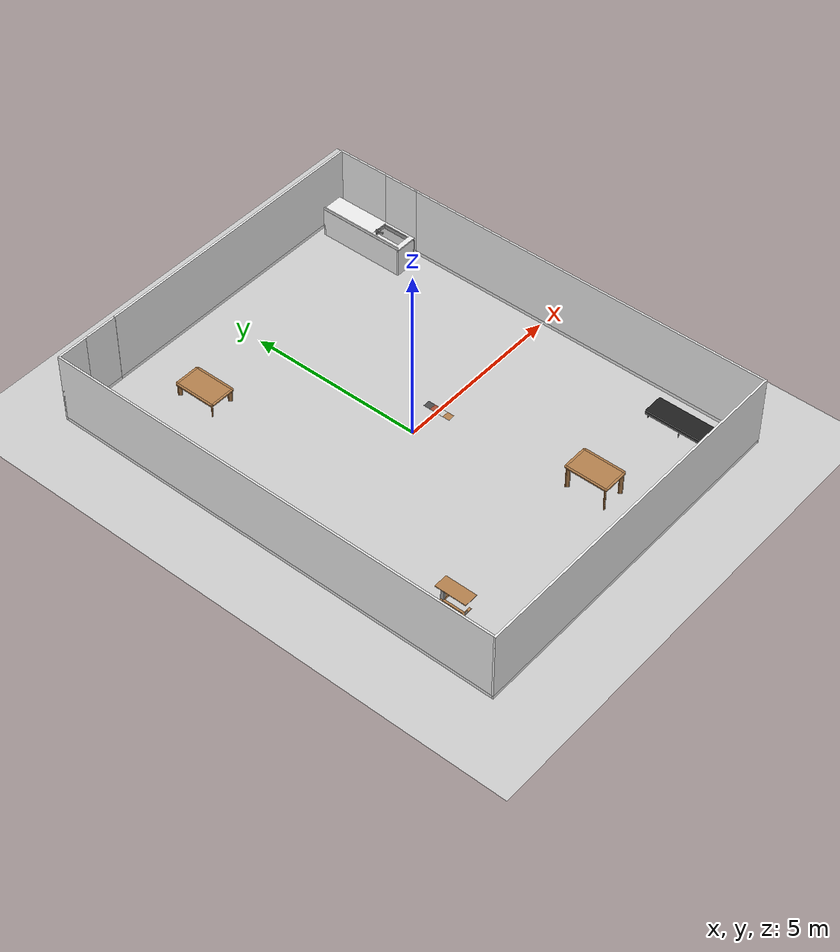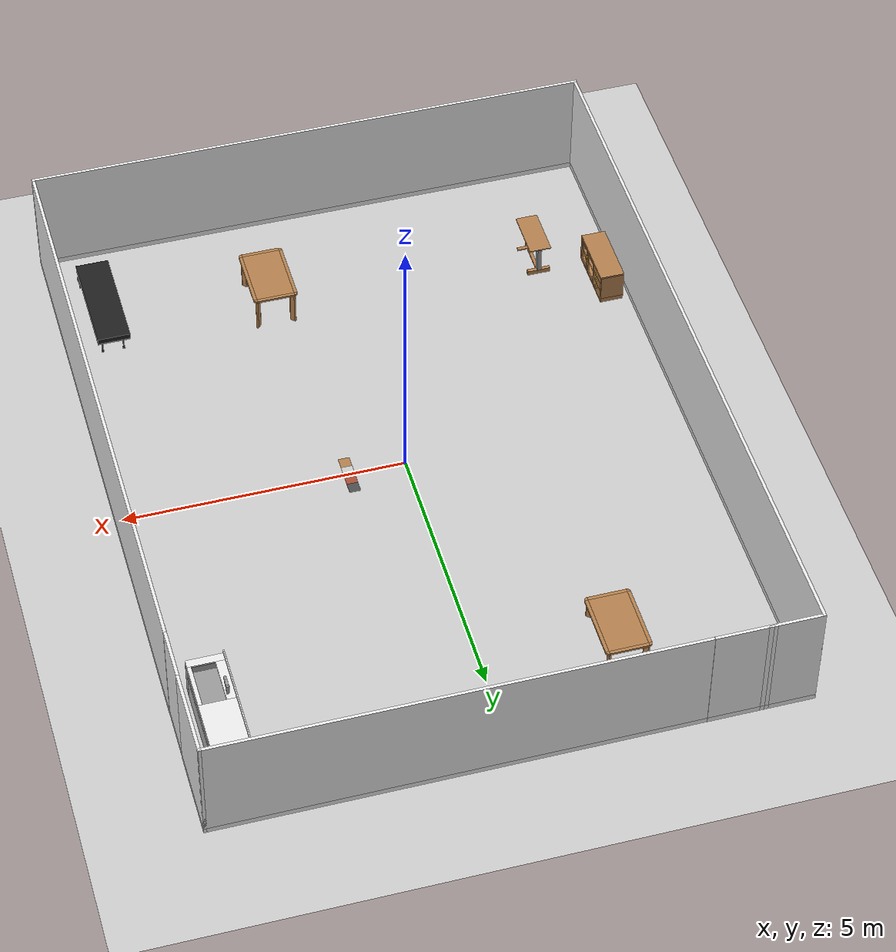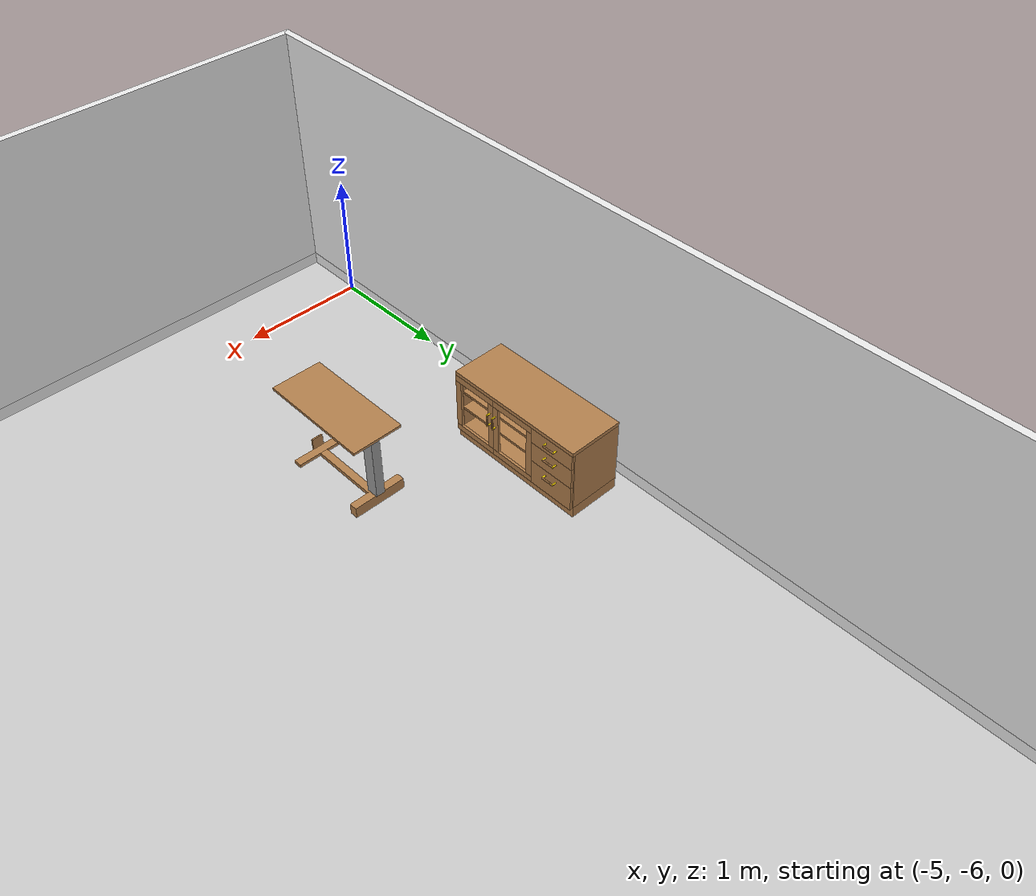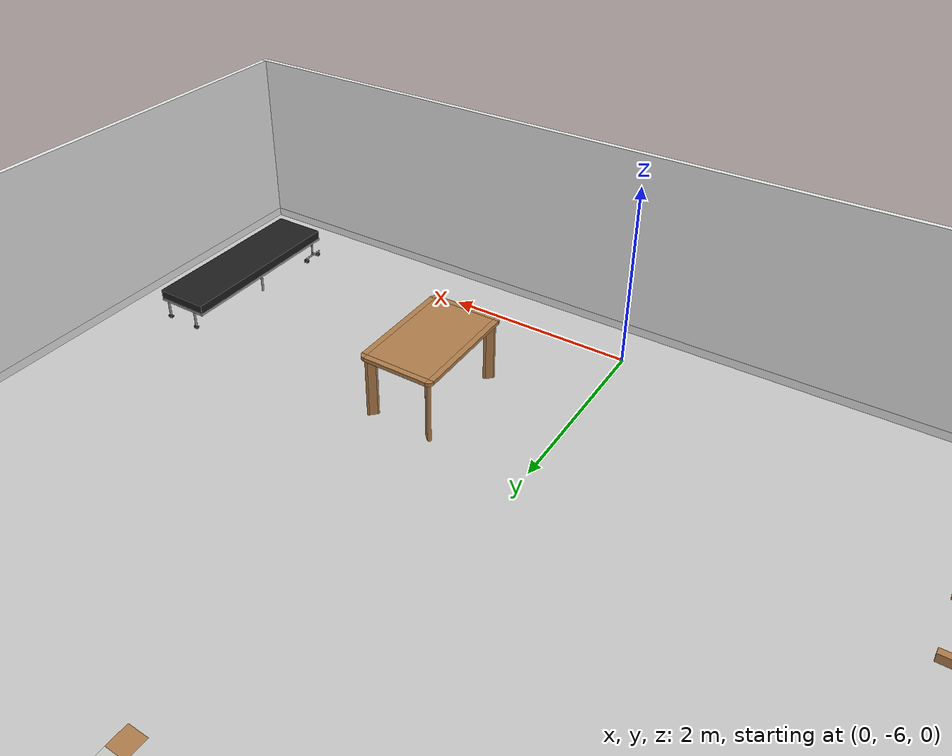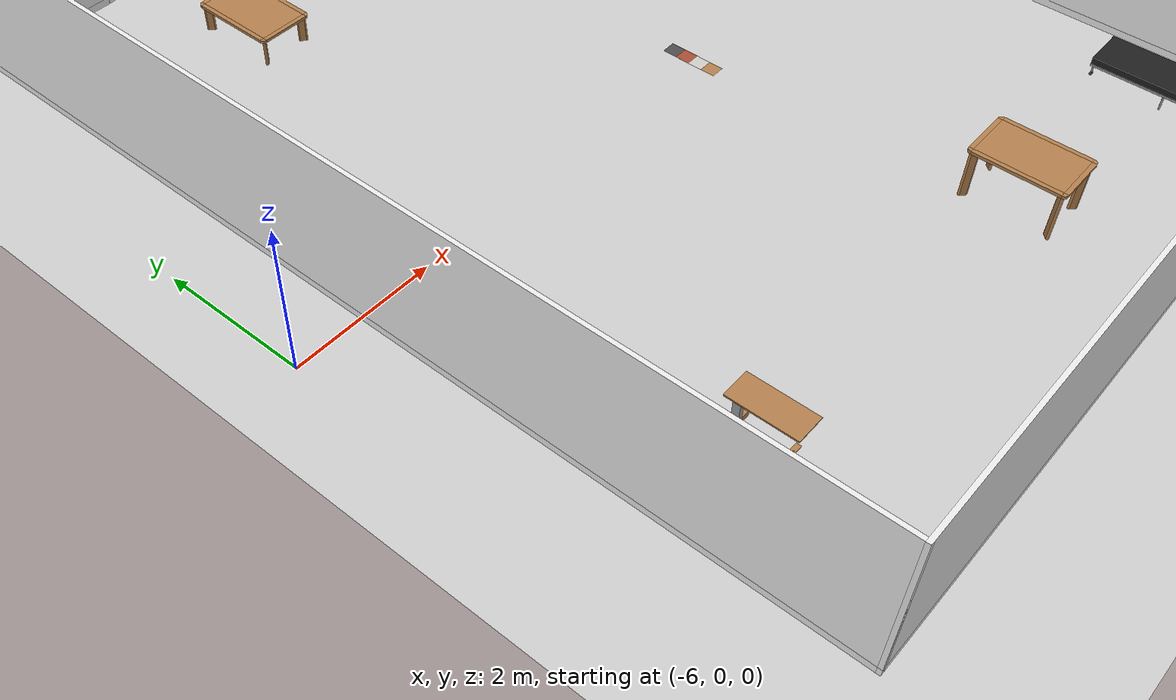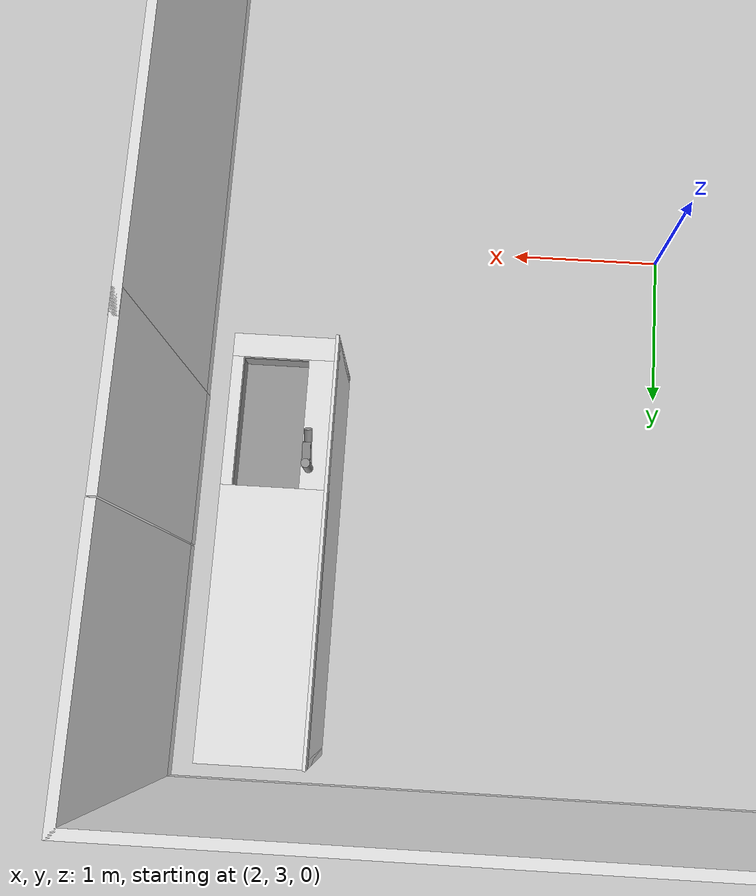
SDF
<sdf version="1.6">
 <world name="megaweb">
  <physics name="default_physics" default="0" type="ode">
   <max_step_size>0.001</max_step_size>
   <real_time_factor>1</real_time_factor>
   <real_time_update_rate>1000</real_time_update_rate>
  </physics>
  <scene><ambient>1 1 1 1</ambient><background>0.7 0.7 0.7 1</background><shadows>0</shadows></scene>
  <model name="ground_plane">
   <static>1</static>
   <link name="link">
    <collision name="collision">
     <geometry><plane><normal>0 0 1</normal><size>100 100</size></plane></geometry>
     <surface><friction><ode><mu>100</mu><mu2>50</mu2></ode></friction></surface>
    </collision>
    <visual name="visual">
     <cast_shadows>0</cast_shadows>
     <geometry><plane><normal>0 0 1</normal><size>100 100</size></plane></geometry>
     <material>
      <script><uri>file://media/materials/scripts/gazebo.material</uri><name>Gazebo/Grey</name></script>
     </material>
    </visual>
   </link>
  </model>
  <light name="floorlight1" type="spot">
   <pose>-3 -3 4 0 -0 0</pose>
   <diffuse>0.8 0.8 0.8 1</diffuse>
   <specular>0.2 0.2 0.2 1</specular>
   <attenuation>
    <range>10</range>
    <constant>0.9</constant>
    <linear>0.2</linear>
    <quadratic>0.001</quadratic>
   </attenuation>
   <spot><inner_angle>0.1</inner_angle><outer_angle>3.14</outer_angle><falloff>0.01</falloff></spot>
   <direction>0 0 -1</direction>
  </light>
  <light name="floorlight2" type="spot">
   <pose>-6 -3 4 0 -0 0</pose>
   <diffuse>0.8 0.8 0.8 1</diffuse>
   <specular>0.2 0.2 0.2 1</specular>
   <attenuation>
    <range>10</range>
    <constant>0.9</constant>
    <linear>0.2</linear>
    <quadratic>0.001</quadratic>
   </attenuation>
   <spot><inner_angle>0.1</inner_angle><outer_angle>3.14</outer_angle><falloff>0.01</falloff></spot>
   <direction>0 0 -1</direction>
  </light>
  <light name="floorlight3" type="spot">
   <pose>-3 -6 4 0 -0 0</pose>
   <diffuse>0.8 0.8 0.8 1</diffuse>
   <specular>0.2 0.2 0.2 1</specular>
   <attenuation>
    <range>10</range>
    <constant>0.9</constant>
    <linear>0.2</linear>
    <quadratic>0.001</quadratic>
   </attenuation>
   <spot><inner_angle>0.1</inner_angle><outer_angle>3.14</outer_angle><falloff>0.01</falloff></spot>
   <direction>0 0 -1</direction>
  </light>
  <light name="floorlight4" type="spot">
   <pose>-6 -6 4 0 -0 0</pose>
   <diffuse>0.8 0.8 0.8 1</diffuse>
   <specular>0.2 0.2 0.2 1</specular>
   <attenuation>
    <range>10</range>
    <constant>0.9</constant>
    <linear>0.2</linear>
    <quadratic>0.001</quadratic>
   </attenuation>
   <spot><inner_angle>0.1</inner_angle><outer_angle>3.14</outer_angle><falloff>0.01</falloff></spot>
   <direction>0 0 -1</direction>
  </light>
  <gravity>0 0 -9.8</gravity>
  <magnetic_field>6e-06 2.3e-05 -4.2e-05</magnetic_field>
  <atmosphere type="adiabatic"/>
  <spherical_coordinates>
   <surface_model>EARTH_WGS84</surface_model>
   <latitude_deg>0</latitude_deg>
   <longitude_deg>0</longitude_deg>
   <elevation>0</elevation>
   <heading_deg>0</heading_deg>
  </spherical_coordinates>
  <model name="full_outside_wall">
   <link name="link">
    <inertial>
     <mass>50</mass>
     <inertia><ixx>1</ixx><ixy>0</ixy><ixz>0</ixz><iyy>1</iyy><iyz>0</iyz><izz>1</izz></inertia>
    </inertial>
    <visual name="x00_13y00_bottom_frame">
     <pose>5.0375 -0.0275 0.05 0 -0 0</pose>
     <geometry><box><size>10.185 0.055 0.1</size></box></geometry>
     <material>
      <script><uri>model://base_materials/color/scripts</uri><name>hsr_color/white</name></script>
     </material>
    </visual>
    <collision name="x00_13y00_collision_bottom_frame">
     <pose>5.0375 -0.0275 0.05 0 -0 0</pose>
     <geometry><box><size>10.185 0.055 0.1</size></box></geometry>
    </collision>
    <visual name="wall_x00_13y00">
     <pose>5.0375 -0.0275 1.095 0 -0 0</pose>
     <geometry><box><size>10.185 0.055 1.99</size></box></geometry>
     <material>
      <script>
       <uri>model://base_materials/wall/scripts</uri>
       <uri>model://base_materials/wall/textures</uri>
       <name>wall/white_noise</name>
      </script>
     </material>
    </visual>
    <collision name="wall_x00_13y00">
     <pose>5.0375 -0.002 1.095 0 -0 0</pose>
     <geometry><box><size>10.08 0.055 1.99</size></box></geometry>
    </collision>
    <visual name="x00y00_15_bottom_frame">
     <pose>-0.0275 6.59 0.05 0 -0 0</pose>
     <geometry><box><size>0.055 13.29 0.1</size></box></geometry>
     <material>
      <script><uri>model://base_materials/color/scripts</uri><name>hsr_color/white</name></script>
     </material>
    </visual>
    <collision name="x00y00_15_collision_bottom_frame">
     <pose>-0.0275 6.59 0.05 0 -0 0</pose>
     <geometry><box><size>0.055 13.29 0.1</size></box></geometry>
    </collision>
    <visual name="wall_x00y00_15">
     <pose>-0.0275 6.59 1.095 0 -0 0</pose>
     <geometry><box><size>0.055 13.29 1.99</size></box></geometry>
     <material>
      <script>
       <uri>model://base_materials/wall/scripts</uri>
       <uri>model://base_materials/wall/textures</uri>
       <name>wall/white_noise</name>
      </script>
     </material>
    </visual>
    <collision name="wall_x00y00_x00y15">
     <pose>-0.002 6.59 1.095 0 -0 0</pose>
     <geometry><box><size>0.002 13.29 1.99</size></box></geometry>
    </collision>
    <visual name="x13y00_12_bottom_frame">
     <pose>10.1025 5.3725 0.05 0 -0 0</pose>
     <geometry><box><size>0.055 10.855 0.1</size></box></geometry>
     <material>
      <script><uri>model://base_materials/color/scripts</uri><name>hsr_color/white</name></script>
     </material>
    </visual>
    <collision name="x13y00_12_collision_bottom_frame">
     <pose>10.1025 5.3725 0.05 0 -0 0</pose>
     <geometry><box><size>0.055 10.855 0.1</size></box></geometry>
    </collision>
    <visual name="wall_x13y00_12">
     <pose>10.1025 5.3725 1.095 0 -0 0</pose>
     <geometry><box><size>0.055 10.855 1.99</size></box></geometry>
     <material>
      <script>
       <uri>model://base_materials/wall/scripts</uri>
       <uri>model://base_materials/wall/textures</uri>
       <name>wall/white_noise</name>
      </script>
     </material>
    </visual>
    <collision name="wall_x13y00_12">
     <pose>10.1025 5.3725 1.095 0 -0 0</pose>
     <geometry><box><size>0.055 10.855 1.99</size></box></geometry>
    </collision>
    <visual name="x13y14_16_bottom_frame">
     <pose>10.1025 12.4675 0.05 0 -0 0</pose>
     <geometry><box><size>0.055 1.535 0.1</size></box></geometry>
     <material>
      <script><uri>model://base_materials/color/scripts</uri><name>hsr_color/white</name></script>
     </material>
    </visual>
    <collision name="x13y14_16_collision_bottom_frame">
     <pose>10.1025 12.4675 0.05 0 -0 0</pose>
     <geometry><box><size>0.055 1.535 0.1</size></box></geometry>
    </collision>
    <visual name="wall_x13y14_x13y16">
     <pose>10.1025 12.4675 1.095 0 -0 0</pose>
     <geometry><box><size>0.055 1.535 1.99</size></box></geometry>
     <material>
      <script>
       <uri>model://base_materials/wall/scripts</uri>
       <uri>model://base_materials/wall/textures</uri>
       <name>wall/white_noise</name>
      </script>
     </material>
    </visual>
    <collision name="wall_x13y14_x13y16">
     <pose>10.1025 12.4675 1.095 0 -0 0</pose>
     <geometry><box><size>0.055 1.535 1.99</size></box></geometry>
    </collision>
    <visual name="x00_01y16_bottom_frame">
     <pose>0.4225 13.2075 0.05 0 -0 0</pose>
     <geometry><box><size>0.955 0.055 0.1</size></box></geometry>
     <material>
      <script><uri>model://base_materials/color/scripts</uri><name>hsr_color/white</name></script>
     </material>
    </visual>
    <collision name="x00_01y16_collision_bottom_frame">
     <pose>0.4225 13.2075 0.05 0 -0 0</pose>
     <geometry><box><size>0.955 0.055 0.1</size></box></geometry>
    </collision>
    <visual name="wall_x00_01y16">
     <pose>0.4225 13.2075 1.095 0 -0 0</pose>
     <geometry><box><size>0.955 0.055 1.99</size></box></geometry>
     <material>
      <script>
       <uri>model://base_materials/wall/scripts</uri>
       <uri>model://base_materials/wall/textures</uri>
       <name>wall/white_noise</name>
      </script>
     </material>
    </visual>
    <collision name="wall_x00_x01y16">
     <pose>0.4225 13.2075 1.095 0 -0 0</pose>
     <geometry><box><size>0.955 0.055 1.99</size></box></geometry>
    </collision>
    <visual name="x03_13y16_bottom_frame">
     <pose>5.965 13.2075 0.05 0 -0 0</pose>
     <geometry><box><size>8.33 0.05 0.1</size></box></geometry>
     <material>
      <script><uri>model://base_materials/color/scripts</uri><name>hsr_color/white</name></script>
     </material>
    </visual>
    <collision name="x03_13y16_collision_bottom_frame">
     <pose>5.965 13.2075 0.05 0 -0 0</pose>
     <geometry><box><size>8.33 0.05 0.1</size></box></geometry>
    </collision>
    <visual name="wall_x03_13y16">
     <pose>5.965 13.2075 1.095 0 -0 0</pose>
     <geometry><box><size>8.33 0.055 1.99</size></box></geometry>
     <material>
      <script>
       <uri>model://base_materials/wall/scripts</uri>
       <uri>model://base_materials/wall/textures</uri>
       <name>wall/white_noise</name>
      </script>
     </material>
    </visual>
    <collision name="wall_x03_13y16">
     <pose>5.965 13.2075 1.095 0 -0 0</pose>
     <geometry><box><size>8.33 0.055 1.99</size></box></geometry>
    </collision>
    <velocity_decay><linear>0</linear><angular>0</angular></velocity_decay>
   </link>
   <static>1</static>
   <pose>-5 -6.5 0 0 -0 0</pose>
  </model>
  <model name="full_wall_55_900_2090">
   <link name="link">
    <inertial>
     <mass>50</mass>
     <inertia><ixx>1</ixx><ixy>0</ixy><ixz>0</ixz><iyy>1</iyy><iyz>0</iyz><izz>1</izz></inertia>
    </inertial>
    <visual name="bottom_frame">
     <pose>0 0 0.05 0 -0 0</pose>
     <geometry><box><size>0.055 1.04 0.1</size></box></geometry>
     <material>
      <script><uri>model://base_materials/color/scripts</uri><name>hsr_color/white</name></script>
     </material>
    </visual>
    <collision name="collision_bottom_frame">
     <pose>0 0 0.05 0 -0 0</pose>
     <geometry><box><size>0.055 1.04 0.1</size></box></geometry>
    </collision>
    <visual name="wall">
     <pose>0 0 1.095 0 -0 0</pose>
     <geometry><box><size>0.055 1.04 1.99</size></box></geometry>
     <material>
      <script>
       <uri>model://base_materials/wall/scripts</uri>
       <uri>model://base_materials/wall/textures</uri>
       <name>wall/white_noise</name>
      </script>
     </material>
    </visual>
    <collision name="collision_wall">
     <pose>0 0 1.095 0 -0 0</pose>
     <geometry><box><size>0.055 1.04 1.99</size></box></geometry>
    </collision>
    <velocity_decay><linear>0</linear><angular>0</angular></velocity_decay>
   </link>
   <static>1</static>
   <pose>5.1 4.67156 0 0 -0 0</pose>
  </model>
  <model name="full_wall_55_900_2090_0">
   <link name="link">
    <inertial>
     <mass>50</mass>
     <inertia><ixx>1</ixx><ixy>0</ixy><ixz>0</ixz><iyy>1</iyy><iyz>0</iyz><izz>1</izz></inertia>
    </inertial>
    <visual name="bottom_frame">
     <pose>0 0 0.05 0 -0 0</pose>
     <geometry><box><size>0.055 1.04 0.1</size></box></geometry>
     <material>
      <script><uri>model://base_materials/color/scripts</uri><name>hsr_color/white</name></script>
     </material>
    </visual>
    <collision name="collision_bottom_frame">
     <pose>0 0 0.05 0 -0 0</pose>
     <geometry><box><size>0.055 1.04 0.1</size></box></geometry>
    </collision>
    <visual name="wall">
     <pose>0 0 1.095 0 -0 0</pose>
     <geometry><box><size>0.055 1.04 1.99</size></box></geometry>
     <material>
      <script>
       <uri>model://base_materials/wall/scripts</uri>
       <uri>model://base_materials/wall/textures</uri>
       <name>wall/white_noise</name>
      </script>
     </material>
    </visual>
    <collision name="collision_wall">
     <pose>0 0 1.095 0 -0 0</pose>
     <geometry><box><size>0.055 1.04 1.99</size></box></geometry>
    </collision>
    <velocity_decay><linear>0</linear><angular>0</angular></velocity_decay>
   </link>
   <static>1</static>
   <pose>-3.72484 6.70714 0 0 -0 1.57</pose>
  </model>
  <model name="class0tag">
   <link name="link">
    <inertial>
     <mass>1</mass>
     <inertia>
      <ixx>0.166667</ixx>
      <ixy>0</ixy>
      <ixz>0</ixz>
      <iyy>0.166667</iyy>
      <iyz>0</iyz>
      <izz>0.166667</izz>
     </inertia>
    </inertial>
    <visual name="visual">
     <geometry><box><size>0.2 0.2 0.0001</size></box></geometry>
     <material>
      <script><name>Gazebo/Wood</name><uri>file://media/materials/scripts/gazebo.material</uri></script>
      <ambient>0.3 0.3 0.3 1</ambient>
      <diffuse>0.7 0.7 0.7 1</diffuse>
      <specular>0.01 0.01 0.01 1</specular>
      <emissive>0 0 0 1</emissive>
      <shader type="vertex"><normal_map>__default__</normal_map></shader>
      <lighting>0</lighting>
     </material>
    </visual>
   </link>
   <static>0</static>
   <pose>1 -0.3 0 0 -0 0</pose>
  </model>
  <model name="class1tag">
   <link name="link">
    <inertial>
     <mass>1</mass>
     <inertia>
      <ixx>0.166667</ixx>
      <ixy>0</ixy>
      <ixz>0</ixz>
      <iyy>0.166667</iyy>
      <iyz>0</iyz>
      <izz>0.166667</izz>
     </inertia>
    </inertial>
    <visual name="visual">
     <geometry><box><size>0.2 0.2 0.0001</size></box></geometry>
     <material>
      <script><name>Gazebo/CeilingTiled</name><uri>file://media/materials/scripts/gazebo.material</uri></script>
      <ambient>0.3 0.3 0.3 1</ambient>
      <diffuse>0.7 0.7 0.7 1</diffuse>
      <specular>0.01 0.01 0.01 1</specular>
      <emissive>0 0 0 1</emissive>
      <shader type="vertex"><normal_map>__default__</normal_map></shader>
      <lighting>0</lighting>
     </material>
    </visual>
   </link>
   <static>0</static>
   <pose>1 -0.1 0 0 -0 0</pose>
  </model>
  <model name="class2tag">
   <link name="link">
    <inertial>
     <mass>1</mass>
     <inertia>
      <ixx>0.166667</ixx>
      <ixy>0</ixy>
      <ixz>0</ixz>
      <iyy>0.166667</iyy>
      <iyz>0</iyz>
      <izz>0.166667</izz>
     </inertia>
    </inertial>
    <visual name="visual">
     <geometry><box><size>0.2 0.2 0.0001</size></box></geometry>
     <material>
      <script><name>Gazebo/Bricks</name><uri>file://media/materials/scripts/gazebo.material</uri></script>
      <ambient>0.3 0.3 0.3 1</ambient>
      <diffuse>0.7 0.7 0.7 1</diffuse>
      <specular>0.01 0.01 0.01 1</specular>
      <emissive>0 0 0 1</emissive>
      <shader type="vertex"><normal_map>__default__</normal_map></shader>
      <lighting>0</lighting>
     </material>
    </visual>
   </link>
   <static>0</static>
   <pose>1 0.1 0 0 -0 0</pose>
  </model>
  <model name="class3tag">
   <link name="link">
    <inertial>
     <mass>1</mass>
     <inertia>
      <ixx>0.166667</ixx>
      <ixy>0</ixy>
      <ixz>0</ixz>
      <iyy>0.166667</iyy>
      <iyz>0</iyz>
      <izz>0.166667</izz>
     </inertia>
    </inertial>
    <visual name="visual">
     <geometry><box><size>0.2 0.2 0.0001</size></box></geometry>
     <material>
      <script><name>Gazebo/Road</name><uri>file://media/materials/scripts/gazebo.material</uri></script>
      <ambient>0.3 0.3 0.3 1</ambient>
      <diffuse>0.7 0.7 0.7 1</diffuse>
      <specular>0.01 0.01 0.01 1</specular>
      <emissive>0 0 0 1</emissive>
      <shader type="vertex"><normal_map>__default__</normal_map></shader>
      <lighting>0</lighting>
     </material>
    </visual>
   </link>
   <static>0</static>
   <pose>1 0.3 0 0 -0 0</pose>
  </model>
  <model name="living_sideboard">
   <link name="link">
    <inertial>
     <mass>10</mass>
     <inertia><ixx>1</ixx><ixy>0</ixy><ixz>0</ixz><iyy>1</iyy><iyz>0</iyz><izz>1</izz></inertia>
    </inertial>
    <visual name="left_board">
     <pose>-0.23 0.01 0.3375 0 -0 0</pose>
     <geometry><box><size>0.42 0.02 0.495</size></box></geometry>
     <material>
      <script><uri>model://base_materials/wood/scripts/wood.material</uri><name>base_materials/wood</name></script>
     </material>
    </visual>
    <collision name="collision_left_board">
     <pose>-0.23 0.01 0.3375 0 -0 0</pose>
     <geometry><box><size>0.42 0.02 0.495</size></box></geometry>
    </collision>
    <visual name="back_board">
     <pose>-0.42 0.575 0.2925 0 -0 0</pose>
     <geometry><box><size>0.02 1.11 0.585</size></box></geometry>
     <material>
      <script><uri>model://base_materials/wood/scripts/wood.material</uri><name>base_materials/wood</name></script>
     </material>
    </visual>
    <collision name="collision_back_board">
     <pose>-0.42 0.575 0.2925 0 -0 0</pose>
     <geometry><box><size>0.02 1.11 0.585</size></box></geometry>
    </collision>
    <visual name="right_board">
     <pose>-0.23 1.14 0.3375 0 -0 0</pose>
     <geometry><box><size>0.42 0.02 0.495</size></box></geometry>
     <material>
      <script><uri>model://base_materials/wood/scripts/wood.material</uri><name>base_materials/wood</name></script>
     </material>
    </visual>
    <collision name="collision_right_board">
     <pose>-0.23 1.14 0.3375 0 -0 0</pose>
     <geometry><box><size>0.42 0.02 0.495</size></box></geometry>
    </collision>
    <visual name="center_vertical_board1">
     <pose>-0.23 0.74 0.3375 0 -0 0</pose>
     <geometry><box><size>0.42 0.02 0.495</size></box></geometry>
     <material>
      <script><uri>model://base_materials/wood/scripts/wood.material</uri><name>base_materials/wood</name></script>
     </material>
    </visual>
    <collision name="collision_center_vertical_board1">
     <pose>-0.23 0.74 0.3375 0 -0 0</pose>
     <geometry><box><size>0.42 0.02 0.495</size></box></geometry>
    </collision>
    <visual name="top_board">
     <pose>-0.22 0.575 0.6 0 -0 0</pose>
     <geometry><box><size>0.44 1.15 0.03</size></box></geometry>
     <material>
      <script><uri>model://base_materials/wood/scripts/wood.material</uri><name>base_materials/wood</name></script>
     </material>
    </visual>
    <collision name="collision_top_board">
     <pose>-0.22 0.575 0.6 0 -0 0</pose>
     <geometry><box><size>0.44 1.15 0.03</size></box></geometry>
    </collision>
    <visual name="bottom_board">
     <pose>-0.23 0.575 0.045 0 -0 0</pose>
     <geometry><box><size>0.42 1.15 0.09</size></box></geometry>
     <material>
      <script><uri>model://base_materials/wood/scripts/wood.material</uri><name>base_materials/wood</name></script>
     </material>
    </visual>
    <collision name="collision_bottom_board">
     <pose>-0.23 0.575 0.045 0 -0 0</pose>
     <geometry><box><size>0.42 1.15 0.09</size></box></geometry>
    </collision>
    <visual name="1st_shelf">
     <pose>-0.225 0.37 0.259 0 -0 0</pose>
     <geometry><box><size>0.36 0.72 0.018</size></box></geometry>
     <material>
      <script><uri>model://base_materials/wood/scripts/wood.material</uri><name>base_materials/wood</name></script>
     </material>
    </visual>
    <collision name="collision_1st_shelf">
     <pose>-0.225 0.37 0.259 0 -0 0</pose>
     <geometry><box><size>0.36 0.72 0.018</size></box></geometry>
    </collision>
    <visual name="2nd_shelf">
     <pose>-0.225 0.37 0.407 0 -0 0</pose>
     <geometry><box><size>0.36 0.72 0.018</size></box></geometry>
     <material>
      <script><uri>model://base_materials/wood/scripts/wood.material</uri><name>base_materials/wood</name></script>
     </material>
    </visual>
    <collision name="collision_2nd_shelf">
     <pose>-0.225 0.37 0.407 0 -0 0</pose>
     <geometry><box><size>0.36 0.72 0.018</size></box></geometry>
    </collision>
    <visual name="1st_drawer">
     <pose>-0.2025 0.95 0.52 0 -0 0</pose>
     <geometry><box><size>0.405 0.38 0.13</size></box></geometry>
     <material>
      <script><uri>model://base_materials/wood/scripts/wood.material</uri><name>base_materials/wood</name></script>
     </material>
    </visual>
    <collision name="collision_1st_drawer">
     <pose>-0.2025 0.95 0.52 0 -0 0</pose>
     <geometry><box><size>0.405 0.38 0.13</size></box></geometry>
    </collision>
    <visual name="1st_drawer_handle_l1">
     <pose>0.015 0.9015 0.535 3.14159 1.57079 3.14159</pose>
     <geometry><cylinder><radius>0.006</radius><length>0.03</length></cylinder></geometry>
     <material>
      <ambient>1 0.84314 0 1</ambient>
      <diffuse>1 0.84314 0 1</diffuse>
      <specular>0.1 0.1 0.1 1</specular>
     </material>
    </visual>
    <collision name="collision_1st_drawer_handle_l1">
     <pose>0.015 0.9015 0.535 3.14159 1.57079 3.14159</pose>
     <geometry><cylinder><radius>0.006</radius><length>0.03</length></cylinder></geometry>
    </collision>
    <visual name="1st_drawer_handle_l2">
     <pose>0.03 0.9015 0.535 0 -0 0</pose>
     <geometry><sphere><radius>0.006</radius></sphere></geometry>
     <material>
      <ambient>1 0.84314 0 1</ambient>
      <diffuse>1 0.84314 0 1</diffuse>
      <specular>0.1 0.1 0.1 1</specular>
     </material>
    </visual>
    <collision name="collision_1st_drawer_handle_l2">
     <pose>0.03 0.9015 0.535 0 -0 0</pose>
     <geometry><sphere><radius>0.006</radius></sphere></geometry>
    </collision>
    <visual name="1st_drawer_handle_r1">
     <pose>0.015 0.9985 0.535 3.14159 1.57079 3.14159</pose>
     <geometry><cylinder><radius>0.006</radius><length>0.03</length></cylinder></geometry>
     <material>
      <ambient>1 0.84314 0 1</ambient>
      <diffuse>1 0.84314 0 1</diffuse>
      <specular>0.1 0.1 0.1 1</specular>
     </material>
    </visual>
    <collision name="collision_1st_drawer_handle_r1">
     <pose>0.015 0.9985 0.535 3.14159 1.57079 3.14159</pose>
     <geometry><cylinder><radius>0.006</radius><length>0.03</length></cylinder></geometry>
    </collision>
    <visual name="1st_drawer_handle_r2">
     <pose>0.03 0.9985 0.535 0 -0 0</pose>
     <geometry><sphere><radius>0.006</radius></sphere></geometry>
     <material>
      <ambient>1 0.84314 0 1</ambient>
      <diffuse>1 0.84314 0 1</diffuse>
      <specular>0.1 0.1 0.1 1</specular>
     </material>
    </visual>
    <collision name="collision_1st_drawer_handle_r2">
     <pose>0.03 0.9985 0.535 0 -0 0</pose>
     <geometry><sphere><radius>0.006</radius></sphere></geometry>
    </collision>
    <visual name="1st_drawer_handle_center">
     <pose>0.03 0.95 0.535 1.5708 -0 0</pose>
     <geometry><cylinder><radius>0.006</radius><length>0.097</length></cylinder></geometry>
     <material>
      <script><uri>model://base_materials/wood/scripts/wood.material</uri><name>base_materials/wood</name></script>
     </material>
    </visual>
    <collision name="collision_1st_drawer_handle_center">
     <pose>0.03 0.95 0.535 1.5708 -0 0</pose>
     <geometry><cylinder><radius>0.006</radius><length>0.097</length></cylinder></geometry>
    </collision>
    <visual name="2nd_drawer">
     <pose>-0.2025 0.95 0.37 0 -0 0</pose>
     <geometry><box><size>0.405 0.38 0.17</size></box></geometry>
     <material>
      <script><uri>model://base_materials/wood/scripts/wood.material</uri><name>base_materials/wood</name></script>
     </material>
    </visual>
    <collision name="collision_2nd_drawer">
     <pose>-0.2025 0.95 0.37 0 -0 0</pose>
     <geometry><box><size>0.405 0.38 0.17</size></box></geometry>
    </collision>
    <visual name="2nd_drawer_handle_l1">
     <pose>0.015 0.9015 0.405 3.14159 1.57079 3.14159</pose>
     <geometry><cylinder><radius>0.006</radius><length>0.03</length></cylinder></geometry>
     <material>
      <ambient>1 0.84314 0 1</ambient>
      <diffuse>1 0.84314 0 1</diffuse>
      <specular>0.1 0.1 0.1 1</specular>
     </material>
    </visual>
    <collision name="collision_2nd_drawer_handle_l1">
     <pose>0.015 0.9015 0.405 3.14159 1.57079 3.14159</pose>
     <geometry><cylinder><radius>0.006</radius><length>0.03</length></cylinder></geometry>
    </collision>
    <visual name="2nd_drawer_handle_l2">
     <pose>0.03 0.9015 0.405 0 -0 0</pose>
     <geometry><sphere><radius>0.006</radius></sphere></geometry>
     <material>
      <ambient>1 0.84314 0 1</ambient>
      <diffuse>1 0.84314 0 1</diffuse>
      <specular>0.1 0.1 0.1 1</specular>
     </material>
    </visual>
    <collision name="collision_2nd_drawer_handle_l2">
     <pose>0.03 0.9015 0.405 0 -0 0</pose>
     <geometry><sphere><radius>0.006</radius></sphere></geometry>
    </collision>
    <visual name="2nd_drawer_handle_r1">
     <pose>0.015 0.9985 0.405 3.14159 1.57079 3.14159</pose>
     <geometry><cylinder><radius>0.006</radius><length>0.03</length></cylinder></geometry>
     <material>
      <ambient>1 0.84314 0 1</ambient>
      <diffuse>1 0.84314 0 1</diffuse>
      <specular>0.1 0.1 0.1 1</specular>
     </material>
    </visual>
    <collision name="collision_2nd_drawer_handle_r1">
     <pose>0.015 0.9985 0.405 3.14159 1.57079 3.14159</pose>
     <geometry><cylinder><radius>0.006</radius><length>0.03</length></cylinder></geometry>
    </collision>
    <visual name="2nd_drawer_handle_r2">
     <pose>0.03 0.9985 0.405 0 -0 0</pose>
     <geometry><sphere><radius>0.006</radius></sphere></geometry>
     <material>
      <ambient>1 0.84314 0 1</ambient>
      <diffuse>1 0.84314 0 1</diffuse>
      <specular>0.1 0.1 0.1 1</specular>
     </material>
    </visual>
    <collision name="collision_2nd_drawer_handle_r2">
     <pose>0.03 0.9985 0.405 0 -0 0</pose>
     <geometry><sphere><radius>0.006</radius></sphere></geometry>
    </collision>
    <visual name="2nd_drawer_handle_center">
     <pose>0.03 0.95 0.405 1.5708 -0 0</pose>
     <geometry><cylinder><radius>0.006</radius><length>0.097</length></cylinder></geometry>
     <material>
      <script><uri>model://base_materials/wood/scripts/wood.material</uri><name>base_materials/wood</name></script>
     </material>
    </visual>
    <collision name="collision_2nd_drawer_handle_center">
     <pose>0.03 0.95 0.405 1.5708 -0 0</pose>
     <geometry><cylinder><radius>0.006</radius><length>0.097</length></cylinder></geometry>
    </collision>
    <visual name="3rd_drawer">
     <pose>-0.2025 0.95 0.18 0 -0 0</pose>
     <geometry><box><size>0.405 0.38 0.21</size></box></geometry>
     <material>
      <script><uri>model://base_materials/wood/scripts/wood.material</uri><name>base_materials/wood</name></script>
     </material>
    </visual>
    <collision name="collision_3rd_drawer">
     <pose>-0.2025 0.95 0.18 0 -0 0</pose>
     <geometry><box><size>0.405 0.38 0.21</size></box></geometry>
    </collision>
    <visual name="3rd_drawer_handle_l1">
     <pose>0.015 0.9015 0.235 3.14159 1.57079 3.14159</pose>
     <geometry><cylinder><radius>0.006</radius><length>0.03</length></cylinder></geometry>
     <material>
      <ambient>1 0.84314 0 1</ambient>
      <diffuse>1 0.84314 0 1</diffuse>
      <specular>0.1 0.1 0.1 1</specular>
     </material>
    </visual>
    <collision name="collision_3rd_drawer_handle_l1">
     <pose>0.015 0.9015 0.235 3.14159 1.57079 3.14159</pose>
     <geometry><cylinder><radius>0.006</radius><length>0.03</length></cylinder></geometry>
    </collision>
    <visual name="3rd_drawer_handle_l2">
     <pose>0.03 0.9015 0.235 0 -0 0</pose>
     <geometry><sphere><radius>0.006</radius></sphere></geometry>
     <material>
      <ambient>1 0.84314 0 1</ambient>
      <diffuse>1 0.84314 0 1</diffuse>
      <specular>0.1 0.1 0.1 1</specular>
     </material>
    </visual>
    <collision name="collision_3rd_drawer_handle_l2">
     <pose>0.03 0.9015 0.235 0 -0 0</pose>
     <geometry><sphere><radius>0.006</radius></sphere></geometry>
    </collision>
    <visual name="3rd_drawer_handle_r1">
     <pose>0.015 0.9985 0.235 3.14159 1.57079 3.14159</pose>
     <geometry><cylinder><radius>0.006</radius><length>0.03</length></cylinder></geometry>
     <material>
      <ambient>1 0.84314 0 1</ambient>
      <diffuse>1 0.84314 0 1</diffuse>
      <specular>0.1 0.1 0.1 1</specular>
     </material>
    </visual>
    <collision name="collision_3rd_drawer_handle_r1">
     <pose>0.015 0.9985 0.235 3.14159 1.57079 3.14159</pose>
     <geometry><cylinder><radius>0.006</radius><length>0.03</length></cylinder></geometry>
    </collision>
    <visual name="3rd_drawer_handle_r2">
     <pose>0.03 0.9985 0.235 0 -0 0</pose>
     <geometry><sphere><radius>0.006</radius></sphere></geometry>
     <material>
      <ambient>1 0.84314 0 1</ambient>
      <diffuse>1 0.84314 0 1</diffuse>
      <specular>0.1 0.1 0.1 1</specular>
     </material>
    </visual>
    <collision name="collision_3rd_drawer_handle_r2">
     <pose>0.03 0.9985 0.235 0 -0 0</pose>
     <geometry><sphere><radius>0.006</radius></sphere></geometry>
    </collision>
    <visual name="3rd_drawer_handle_center">
     <pose>0.03 0.95 0.235 1.5708 -0 0</pose>
     <geometry><cylinder><radius>0.006</radius><length>0.097</length></cylinder></geometry>
     <material>
      <script><uri>model://base_materials/wood/scripts/wood.material</uri><name>base_materials/wood</name></script>
     </material>
    </visual>
    <collision name="collision_3rd_drawer_handle_center">
     <pose>0.03 0.95 0.235 1.5708 -0 0</pose>
     <geometry><cylinder><radius>0.006</radius><length>0.097</length></cylinder></geometry>
    </collision>
    <visual name="left_door_left_frame">
     <pose>-0.01 0.025 0.3275 0 -0 0</pose>
     <geometry><box><size>0.02 0.05 0.405</size></box></geometry>
     <material>
      <script><uri>model://base_materials/wood/scripts/wood.material</uri><name>base_materials/wood</name></script>
     </material>
    </visual>
    <collision name="collision_left_door_left_frame">
     <pose>-0.01 0.025 0.3275 0 -0 0</pose>
     <geometry><box><size>0.02 0.05 0.405</size></box></geometry>
    </collision>
    <visual name="left_door_right_frame">
     <pose>-0.01 0.355 0.3275 0 -0 0</pose>
     <geometry><box><size>0.02 0.05 0.405</size></box></geometry>
     <material>
      <script><uri>model://base_materials/wood/scripts/wood.material</uri><name>base_materials/wood</name></script>
     </material>
    </visual>
    <collision name="collision_left_door_right_frame">
     <pose>-0.01 0.355 0.3275 0 -0 0</pose>
     <geometry><box><size>0.02 0.05 0.405</size></box></geometry>
    </collision>
    <visual name="left_door_handle_top1">
     <pose>0.015 0.355 0.4475 3.14159 1.57079 3.14159</pose>
     <geometry><cylinder><radius>0.006</radius><length>0.03</length></cylinder></geometry>
     <material>
      <ambient>1 0.84314 0 1</ambient>
      <diffuse>1 0.84314 0 1</diffuse>
      <specular>0.1 0.1 0.1 1</specular>
     </material>
    </visual>
    <collision name="collision_left_door_handle_top1">
     <pose>0.015 0.355 0.4475 3.14159 1.57079 3.14159</pose>
     <geometry><cylinder><radius>0.006</radius><length>0.03</length></cylinder></geometry>
    </collision>
    <visual name="left_door_handle_top2">
     <pose>0.03 0.355 0.4475 0 -0 0</pose>
     <geometry><sphere><radius>0.006</radius></sphere></geometry>
     <material>
      <ambient>1 0.84314 0 1</ambient>
      <diffuse>1 0.84314 0 1</diffuse>
      <specular>0.1 0.1 0.1 1</specular>
     </material>
    </visual>
    <collision name="collision_left_door_handle_top2">
     <pose>0.03 0.355 0.4475 0 -0 0</pose>
     <geometry><sphere><radius>0.006</radius></sphere></geometry>
    </collision>
    <visual name="left_door_handle_bottom1">
     <pose>0.015 0.355 0.3505 3.14159 1.57079 3.14159</pose>
     <geometry><cylinder><radius>0.006</radius><length>0.03</length></cylinder></geometry>
     <material>
      <ambient>1 0.84314 0 1</ambient>
      <diffuse>1 0.84314 0 1</diffuse>
      <specular>0.1 0.1 0.1 1</specular>
     </material>
    </visual>
    <collision name="collision_left_door_handle_bottom1">
     <pose>0.015 0.355 0.3505 3.14159 1.57079 3.14159</pose>
     <geometry><cylinder><radius>0.006</radius><length>0.03</length></cylinder></geometry>
    </collision>
    <visual name="left_door_handle_bottom2">
     <pose>0.03 0.355 0.3505 0 -0 0</pose>
     <geometry><sphere><radius>0.006</radius></sphere></geometry>
     <material>
      <ambient>1 0.84314 0 1</ambient>
      <diffuse>1 0.84314 0 1</diffuse>
      <specular>0.1 0.1 0.1 1</specular>
     </material>
    </visual>
    <collision name="collision_left_door_handle_bottom2">
     <pose>0.03 0.355 0.3505 0 -0 0</pose>
     <geometry><sphere><radius>0.006</radius></sphere></geometry>
    </collision>
    <visual name="left_door_handle_center">
     <pose>0.03 0.355 0.399 0 -0 0</pose>
     <geometry><cylinder><radius>0.006</radius><length>0.097</length></cylinder></geometry>
     <material>
      <script><uri>model://base_materials/wood/scripts/wood.material</uri><name>base_materials/wood</name></script>
     </material>
    </visual>
    <collision name="collision_left_door_handle_center">
     <pose>0.03 0.355 0.399 0 -0 0</pose>
     <geometry><cylinder><radius>0.006</radius><length>0.097</length></cylinder></geometry>
    </collision>
    <visual name="left_door_top_frame">
     <pose>-0.01 0.19 0.5575 0 -0 0</pose>
     <geometry><box><size>0.02 0.38 0.055</size></box></geometry>
     <material>
      <script><uri>model://base_materials/wood/scripts/wood.material</uri><name>base_materials/wood</name></script>
     </material>
    </visual>
    <collision name="collision_left_door_top_frame">
     <pose>-0.01 0.19 0.5575 0 -0 0</pose>
     <geometry><box><size>0.02 0.38 0.055</size></box></geometry>
    </collision>
    <visual name="left_door_bottom_frame">
     <pose>-0.01 0.19 0.1 0 -0 0</pose>
     <geometry><box><size>0.02 0.38 0.05</size></box></geometry>
     <material>
      <script><uri>model://base_materials/wood/scripts/wood.material</uri><name>base_materials/wood</name></script>
     </material>
    </visual>
    <collision name="collision_left_door_bottom_frame">
     <pose>-0.01 0.19 0.1 0 -0 0</pose>
     <geometry><box><size>0.02 0.38 0.05</size></box></geometry>
    </collision>
    <visual name="right_door_left_frame">
     <pose>-0.01 0.405 0.3275 0 -0 0</pose>
     <geometry><box><size>0.02 0.05 0.405</size></box></geometry>
     <material>
      <script><uri>model://base_materials/wood/scripts/wood.material</uri><name>base_materials/wood</name></script>
     </material>
    </visual>
    <collision name="collision_right_door_left_frame">
     <pose>-0.01 0.405 0.3275 0 -0 0</pose>
     <geometry><box><size>0.02 0.05 0.405</size></box></geometry>
    </collision>
    <visual name="right_door_right_frame">
     <pose>-0.01 0.735 0.3275 0 -0 0</pose>
     <geometry><box><size>0.02 0.05 0.405</size></box></geometry>
     <material>
      <script><uri>model://base_materials/wood/scripts/wood.material</uri><name>base_materials/wood</name></script>
     </material>
    </visual>
    <collision name="collision_right_door_right_frame">
     <pose>-0.01 0.735 0.3275 0 -0 0</pose>
     <geometry><box><size>0.02 0.05 0.405</size></box></geometry>
    </collision>
    <visual name="right_door_top_frame">
     <pose>-0.01 0.57 0.5575 0 -0 0</pose>
     <geometry><box><size>0.02 0.38 0.055</size></box></geometry>
     <material>
      <script><uri>model://base_materials/wood/scripts/wood.material</uri><name>base_materials/wood</name></script>
     </material>
    </visual>
    <collision name="collision_right_door_top_frame">
     <pose>-0.01 0.57 0.5575 0 -0 0</pose>
     <geometry><box><size>0.02 0.38 0.055</size></box></geometry>
    </collision>
    <visual name="right_door_bottom_frame">
     <pose>-0.01 0.57 0.1 0 -0 0</pose>
     <geometry><box><size>0.02 0.38 0.05</size></box></geometry>
     <material>
      <script><uri>model://base_materials/wood/scripts/wood.material</uri><name>base_materials/wood</name></script>
     </material>
    </visual>
    <collision name="collision_right_door_bottom_frame">
     <pose>-0.01 0.57 0.1 0 -0 0</pose>
     <geometry><box><size>0.02 0.38 0.05</size></box></geometry>
    </collision>
    <visual name="right_door_handle_top1">
     <pose>0.015 0.405 0.4475 3.14159 1.57079 3.14159</pose>
     <geometry><cylinder><radius>0.006</radius><length>0.03</length></cylinder></geometry>
     <material>
      <ambient>1 0.84314 0 1</ambient>
      <diffuse>1 0.84314 0 1</diffuse>
      <specular>0.1 0.1 0.1 1</specular>
     </material>
    </visual>
    <collision name="collision_right_door_handle_top1">
     <pose>0.015 0.405 0.4475 3.14159 1.57079 3.14159</pose>
     <geometry><cylinder><radius>0.006</radius><length>0.03</length></cylinder></geometry>
    </collision>
    <visual name="right_door_handle_top2">
     <pose>0.03 0.405 0.4475 0 -0 0</pose>
     <geometry><sphere><radius>0.006</radius></sphere></geometry>
     <material>
      <ambient>1 0.84314 0 1</ambient>
      <diffuse>1 0.84314 0 1</diffuse>
      <specular>0.1 0.1 0.1 1</specular>
     </material>
    </visual>
    <collision name="collision_right_door_handle_top2">
     <pose>0.03 0.405 0.4475 0 -0 0</pose>
     <geometry><sphere><radius>0.006</radius></sphere></geometry>
    </collision>
    <visual name="right_door_handle_bottom1">
     <pose>0.015 0.405 0.3505 3.14159 1.57079 3.14159</pose>
     <geometry><cylinder><radius>0.006</radius><length>0.03</length></cylinder></geometry>
     <material>
      <ambient>1 0.84314 0 1</ambient>
      <diffuse>1 0.84314 0 1</diffuse>
      <specular>0.1 0.1 0.1 1</specular>
     </material>
    </visual>
    <collision name="collision_right_door_handle_bottom1">
     <pose>0.015 0.405 0.3505 3.14159 1.57079 3.14159</pose>
     <geometry><cylinder><radius>0.006</radius><length>0.03</length></cylinder></geometry>
    </collision>
    <visual name="right_door_handle_bottom2">
     <pose>0.03 0.405 0.3505 0 -0 0</pose>
     <geometry><sphere><radius>0.006</radius></sphere></geometry>
     <material>
      <ambient>1 0.84314 0 1</ambient>
      <diffuse>1 0.84314 0 1</diffuse>
      <specular>0.1 0.1 0.1 1</specular>
     </material>
    </visual>
    <collision name="collision_right_door_handle_bottom2">
     <pose>0.03 0.405 0.3505 0 -0 0</pose>
     <geometry><sphere><radius>0.006</radius></sphere></geometry>
    </collision>
    <visual name="right_door_handle_center">
     <pose>0.03 0.405 0.399 0 -0 0</pose>
     <geometry><cylinder><radius>0.006</radius><length>0.097</length></cylinder></geometry>
     <material>
      <script><uri>model://base_materials/wood/scripts/wood.material</uri><name>base_materials/wood</name></script>
     </material>
    </visual>
    <collision name="collision_right_door_handle_center">
     <pose>0.03 0.4 0.399 0 -0 0</pose>
     <geometry><cylinder><radius>0.006</radius><length>0.097</length></cylinder></geometry>
    </collision>
    <velocity_decay><linear>0</linear><angular>0</angular></velocity_decay>
   </link>
   <static>1</static>
   <pose>-4.43738 -4.03045 0 0 -0 0</pose>
  </model>
  <model name="bed_table">
   <link name="link">
    <inertial>
     <pose>0 0.449 0.001 0 -0 0</pose>
     <mass>10</mass>
     <inertia><ixx>1</ixx><ixy>0</ixy><ixz>0</ixz><iyy>1</iyy><iyz>0</iyz><izz>1</izz></inertia>
    </inertial>
    <visual name="top_board">
     <pose>0 0.449 0.625 0 -0 0</pose>
     <geometry><box><size>0.398 0.898 0.02</size></box></geometry>
     <material>
      <script><uri>model://base_materials/wood/scripts/wood.material</uri><name>base_materials/wood</name></script>
     </material>
    </visual>
    <collision name="collision_top_board">
     <pose>0 0.449 0.625 0 -0 0</pose>
     <geometry><box><size>0.398 0.898 0.02</size></box></geometry>
    </collision>
    <visual name="right_pole">
     <pose>0 0.817 0.3515 0 -0 0</pose>
     <geometry><box><size>0.072 0.094 0.527</size></box></geometry>
     <material>
      <script><uri>model://base_materials/color/scripts</uri><name>hsr_color/grey</name></script>
     </material>
    </visual>
    <collision name="collision_right_pole">
     <pose>0 0.817 0.3515 0 -0 0</pose>
     <geometry><box><size>0.072 0.094 0.527</size></box></geometry>
    </collision>
    <visual name="right_bottom_pole">
     <pose>0 0.8225 0.044 0 -0 0</pose>
     <geometry><box><size>0.42 0.063 0.088</size></box></geometry>
     <material>
      <script><uri>model://base_materials/wood/scripts/wood.material</uri><name>base_materials/wood</name></script>
     </material>
    </visual>
    <collision name="collision_right_bottom_pole">
     <pose>0 0.8225 0.044 0 -0 0</pose>
     <geometry><box><size>0.42 0.063 0.088</size></box></geometry>
    </collision>
    <visual name="bottom_center_pole">
     <pose>0 0.502 0.03 0 -0 0</pose>
     <geometry><box><size>0.06 0.578 0.03</size></box></geometry>
     <material>
      <script><uri>model://base_materials/wood/scripts/wood.material</uri><name>base_materials/wood</name></script>
     </material>
    </visual>
    <collision name="collision_bottom_center_pole">
     <pose>0 0.502 0.03 0 -0 0</pose>
     <geometry><box><size>0.06 0.578 0.03</size></box></geometry>
    </collision>
    <visual name="left_bottom_pole">
     <pose>0 0.18 0.0325 0 -0 0</pose>
     <geometry><box><size>0.418 0.066 0.025</size></box></geometry>
     <material>
      <script><uri>model://base_materials/wood/scripts/wood.material</uri><name>base_materials/wood</name></script>
     </material>
    </visual>
    <collision name="collision_left_bottom_pole">
     <pose>0 0.18 0.0325 0 -0 0</pose>
     <geometry><box><size>0.418 0.066 0.025</size></box></geometry>
    </collision>
    <visual name="marker_0010">
     <pose>0 0.14 0.093 0 -0 0</pose>
     <geometry><box><size>0.09 0.001 0.09</size></box></geometry>
     <material>
      <script>
       <uri>model://bed_table/marker/0010/scripts</uri>
       <uri>model://bed_table/marker/0010/textures</uri>
       <name>Marker/0010</name>
      </script>
     </material>
    </visual>
    <collision name="collision_marker_0010">
     <pose>0 0.14 0.093 0 -0 0</pose>
     <geometry><box><size>0.09 0.001 0.09</size></box></geometry>
    </collision>
    <visual name="marker_0010_back_plate">
     <pose>0 0.146 0.093 0 -0 0</pose>
     <geometry><box><size>0.09 0.01 0.09</size></box></geometry>
     <material>
      <script><uri>model://base_materials/wood/scripts/wood.material</uri><name>base_materials/wood</name></script>
     </material>
    </visual>
    <collision name="collision_marker_0010_back_plate">
     <pose>0 0.146 0.093 0 -0 0</pose>
     <geometry><box><size>0.09 0.01 0.09</size></box></geometry>
    </collision>
    <velocity_decay><linear>0</linear><angular>0</angular></velocity_decay>
   </link>
   <static>1</static>
   <pose>-3.60084 -4.75017 0 0 -0 0</pose>
  </model>
  <model name="bed">
   <link name="link">
    <inertial>
     <mass>10</mass>
     <inertia><ixx>1</ixx><ixy>0</ixy><ixz>0</ixz><iyy>1</iyy><iyz>0</iyz><izz>1</izz></inertia>
    </inertial>
    <visual name="cushion">
     <pose>-0.295 -0.975 0.2875 0 -0 0</pose>
     <geometry><box><size>0.59 1.95 0.095</size></box></geometry>
     <material>
      <script>
       <uri>model://base_materials/cloth/scripts</uri>
       <uri>model://base_materials/cloth/textures</uri>
       <name>cloth/black</name>
      </script>
     </material>
    </visual>
    <collision name="collision_cushion">
     <pose>-0.295 -0.975 0.2875 0 -0 0</pose>
     <geometry><box><size>0.59 1.95 0.095</size></box></geometry>
    </collision>
    <visual name="top_frame">
     <pose>-0.295 -0.975 0.225 0 -0 0</pose>
     <geometry><box><size>0.59 1.95 0.03</size></box></geometry>
     <material>
      <script><uri>model://base_materials/color/scripts</uri><name>hsr_color/grey</name></script>
     </material>
    </visual>
    <collision name="collision_top_frame">
     <pose>-0.295 -0.975 0.225 0 -0 0</pose>
     <geometry><box><size>0.59 1.95 0.03</size></box></geometry>
    </collision>
    <visual name="right_front_pole">
     <pose>-0.075 -0.0125 0.125 0 -0 0</pose>
     <geometry><cylinder><radius>0.0125</radius><length>0.17</length></cylinder></geometry>
     <material>
      <script><uri>model://base_materials/color/scripts</uri><name>hsr_color/grey</name></script>
     </material>
    </visual>
    <collision name="collision_right_front_pole">
     <pose>-0.075 -0.0125 0.125 0 -0 0</pose>
     <geometry><cylinder><radius>0.0125</radius><length>0.17</length></cylinder></geometry>
    </collision>
    <visual name="right_front_caster">
     <pose>-0.075 -0.0125 0.02 0 1.57 0</pose>
     <geometry><cylinder><radius>0.02</radius><length>0.04</length></cylinder></geometry>
     <material><script><name>Gazebo/Black</name><uri>__default__</uri></script></material>
    </visual>
    <collision name="collision_right_front_caster">
     <pose>-0.075 -0.0125 0.02 0 1.57 0</pose>
     <geometry><cylinder><radius>0.02</radius><length>0.04</length></cylinder></geometry>
    </collision>
    <visual name="right_back_pole">
     <pose>-0.46 -0.0125 0.125 0 -0 0</pose>
     <geometry><cylinder><radius>0.0125</radius><length>0.17</length></cylinder></geometry>
     <material>
      <script><uri>model://base_materials/color/scripts</uri><name>hsr_color/grey</name></script>
     </material>
    </visual>
    <collision name="collision_right_back_pole">
     <pose>-0.46 -0.0125 0.125 0 -0 0</pose>
     <geometry><cylinder><radius>0.0125</radius><length>0.17</length></cylinder></geometry>
    </collision>
    <visual name="right_back_caster">
     <pose>-0.46 -0.0125 0.02 0 1.57 0</pose>
     <geometry><cylinder><radius>0.02</radius><length>0.04</length></cylinder></geometry>
     <material><script><name>Gazebo/Black</name><uri>__default__</uri></script></material>
    </visual>
    <collision name="collision_back_front_caster">
     <pose>-0.46 -0.0125 0.02 0 1.57 0</pose>
     <geometry><cylinder><radius>0.02</radius><length>0.04</length></cylinder></geometry>
    </collision>
    <visual name="center_front_pole">
     <pose>-0.0425 -0.975 0.105 0 -0 0</pose>
     <geometry><cylinder><radius>0.0125</radius><length>0.21</length></cylinder></geometry>
     <material>
      <script><uri>model://base_materials/color/scripts</uri><name>hsr_color/grey</name></script>
     </material>
    </visual>
    <collision name="collision_center_front_pole">
     <pose>-0.0425 -0.975 0.105 0 -0 0</pose>
     <geometry><cylinder><radius>0.0125</radius><length>0.17</length></cylinder></geometry>
    </collision>
    <visual name="center_back_pole">
     <pose>-0.5475 -0.975 0.105 0 -0 0</pose>
     <geometry><cylinder><radius>0.0125</radius><length>0.21</length></cylinder></geometry>
     <material>
      <script><uri>model://base_materials/color/scripts</uri><name>hsr_color/grey</name></script>
     </material>
    </visual>
    <collision name="collision_center_back_pole">
     <pose>-0.5475 -0.975 0.105 0 -0 0</pose>
     <geometry><cylinder><radius>0.0125</radius><length>0.17</length></cylinder></geometry>
    </collision>
    <visual name="left_front_horizon_pole">
     <pose>-0.01 -1.825 0.06 1.57 -0 0</pose>
     <geometry><cylinder><radius>0.01</radius><length>0.25</length></cylinder></geometry>
     <material>
      <script><uri>model://base_materials/color/scripts</uri><name>hsr_color/grey</name></script>
     </material>
    </visual>
    <collision name="collision_left_front_horizon_pole">
     <pose>-0.01 -1.825 0.06 1.57 -0 0</pose>
     <geometry><cylinder><radius>0.01</radius><length>0.25</length></cylinder></geometry>
    </collision>
    <visual name="left_front_vertical_pole">
     <pose>-0.01 -1.825 0.14 0 -0 0</pose>
     <geometry><cylinder><radius>0.01</radius><length>0.14</length></cylinder></geometry>
     <material>
      <script><uri>model://base_materials/color/scripts</uri><name>hsr_color/grey</name></script>
     </material>
    </visual>
    <collision name="collision_left_front_vertical_pole">
     <pose>-0.01 -1.825 0.14 0 -0 0</pose>
     <geometry><cylinder><radius>0.01</radius><length>0.14</length></cylinder></geometry>
    </collision>
    <visual name="left_front_caster_r">
     <pose>-0.02 -1.725 0.025 0 1.57 0</pose>
     <geometry><cylinder><radius>0.025</radius><length>0.04</length></cylinder></geometry>
     <material><script><name>Gazebo/Black</name><uri>__default__</uri></script></material>
    </visual>
    <collision name="collision_left_front_caster_r">
     <pose>-0.02 -1.725 0.025 0 1.57 0</pose>
     <geometry><cylinder><radius>0.025</radius><length>0.04</length></cylinder></geometry>
    </collision>
    <visual name="left_front_caster_l">
     <pose>-0.02 -1.925 0.025 0 1.57 0</pose>
     <geometry><cylinder><radius>0.025</radius><length>0.04</length></cylinder></geometry>
     <material><script><name>Gazebo/Black</name><uri>__default__</uri></script></material>
    </visual>
    <collision name="collision_left_front_caster_l">
     <pose>-0.02 -1.925 0.025 0 1.57 0</pose>
     <geometry><cylinder><radius>0.025</radius><length>0.04</length></cylinder></geometry>
    </collision>
    <visual name="left_back_horizon_pole">
     <pose>-0.58 -1.825 0.06 1.57 -0 0</pose>
     <geometry><cylinder><radius>0.01</radius><length>0.25</length></cylinder></geometry>
     <material>
      <script><uri>model://base_materials/color/scripts</uri><name>hsr_color/grey</name></script>
     </material>
    </visual>
    <collision name="collision_left_back_horizon_pole">
     <pose>-0.58 -1.825 0.06 1.57 -0 0</pose>
     <geometry><cylinder><radius>0.01</radius><length>0.25</length></cylinder></geometry>
    </collision>
    <visual name="left_back_vertical_pole">
     <pose>-0.58 -1.825 0.14 0 -0 0</pose>
     <geometry><cylinder><radius>0.01</radius><length>0.14</length></cylinder></geometry>
     <material>
      <script><uri>model://base_materials/color/scripts</uri><name>hsr_color/grey</name></script>
     </material>
    </visual>
    <collision name="collision_left_back_vertical_pole">
     <pose>-0.58 -1.825 0.14 0 -0 0</pose>
     <geometry><cylinder><radius>0.01</radius><length>0.14</length></cylinder></geometry>
    </collision>
    <visual name="left_back_caster_r">
     <pose>-0.57 -1.725 0.025 0 1.57 0</pose>
     <geometry><cylinder><radius>0.025</radius><length>0.04</length></cylinder></geometry>
     <material><script><name>Gazebo/Black</name><uri>__default__</uri></script></material>
    </visual>
    <collision name="collision_left_back_caster_r">
     <pose>-0.57 -1.725 0.025 0 1.57 0</pose>
     <geometry><cylinder><radius>0.025</radius><length>0.04</length></cylinder></geometry>
    </collision>
    <visual name="left_back_caster_l">
     <pose>-0.57 -1.925 0.025 0 1.57 0</pose>
     <geometry><cylinder><radius>0.025</radius><length>0.04</length></cylinder></geometry>
     <material><script><name>Gazebo/Black</name><uri>__default__</uri></script></material>
    </visual>
    <collision name="collision_left_back_caster_l">
     <pose>-0.57 -1.925 0.025 0 1.57 0</pose>
     <geometry><cylinder><radius>0.025</radius><length>0.04</length></cylinder></geometry>
    </collision>
    <velocity_decay><linear>0</linear><angular>0</angular></velocity_decay>
   </link>
   <static>1</static>
   <pose>4.56778 -4.01553 0 0 -0 0</pose>
  </model>
  <model name="sink-fix">
   <link name="link">
    <inertial>
     <mass>10</mass>
     <inertia><ixx>1</ixx><ixy>0</ixy><ixz>0</ixz><iyy>1</iyy><iyz>0</iyz><izz>1</izz></inertia>
    </inertial>
    <visual name="faucet1">
     <pose>-0.52 0.82 0.94 0 -0 0</pose>
     <geometry><cylinder><radius>0.027</radius><length>0.18</length></cylinder></geometry>
     <material>
      <script><uri>model://base_materials/color/scripts</uri><name>hsr_color/grey</name></script>
     </material>
    </visual>
    <collision name="collision_faucet1">
     <pose>-0.52 0.82 0.94 0 -0 0</pose>
     <geometry><cylinder><radius>0.027</radius><length>0.18</length></cylinder></geometry>
    </collision>
    <visual name="faucet2">
     <pose>-0.52 0.72 0.97 1.047 -0 0</pose>
     <geometry><cylinder><radius>0.024</radius><length>0.24</length></cylinder></geometry>
     <material>
      <script><uri>model://base_materials/color/scripts</uri><name>hsr_color/grey</name></script>
     </material>
    </visual>
    <collision name="collision_faucet2">
     <pose>-0.52 0.72 0.97 1.047 -0 0</pose>
     <geometry><cylinder><radius>0.024</radius><length>0.24</length></cylinder></geometry>
    </collision>
    <visual name="faucet3">
     <pose>-0.52 0.63 1 0 -0 0</pose>
     <geometry><cylinder><radius>0.015</radius><length>0.04</length></cylinder></geometry>
     <material>
      <script><uri>model://base_materials/color/scripts</uri><name>hsr_color/grey</name></script>
     </material>
    </visual>
    <collision name="collision_faucet3">
     <pose>-0.52 0.63 1 0 -0 0</pose>
     <geometry><cylinder><radius>0.015</radius><length>0.04</length></cylinder></geometry>
    </collision>
    <visual name="faucet_handle">
     <pose>-0.52 0.75 1.03 1.309 -0 0</pose>
     <geometry><box><size>0.048 0.01 0.11</size></box></geometry>
     <material>
      <script><uri>model://base_materials/color/scripts</uri><name>hsr_color/grey</name></script>
     </material>
    </visual>
    <collision name="collision_faucet_handle">
     <pose>-0.52 0.75 1.03 1.309 -0 0</pose>
     <geometry><box><size>0.048 0.01 0.11</size></box></geometry>
    </collision>
    <visual name="back_bucket">
     <pose>-0.57 0.545 0.74 0 -0 0</pose>
     <geometry><box><size>0.02 0.8 0.18</size></box></geometry>
     <material>
      <script><uri>model://base_materials/color/scripts</uri><name>hsr_color/grey</name></script>
     </material>
    </visual>
    <collision name="collision_back_bucket">
     <pose>-0.57 0.545 0.74 0 -0 0</pose>
     <geometry><box><size>0.02 0.8 0.18</size></box></geometry>
    </collision>
    <visual name="front_bucket">
     <pose>-0.06 0.545 0.74 0 -0 0</pose>
     <geometry><box><size>0.02 0.8 0.18</size></box></geometry>
     <material>
      <script><uri>model://base_materials/color/scripts</uri><name>hsr_color/grey</name></script>
     </material>
    </visual>
    <collision name="collision_fromt_bucket">
     <pose>-0.06 0.545 0.74 0 -0 0</pose>
     <geometry><box><size>0.02 0.8 0.18</size></box></geometry>
    </collision>
    <visual name="left_bucket">
     <pose>-0.32 0.14 0.74 0 -0 0</pose>
     <geometry><box><size>0.5 0.02 0.18</size></box></geometry>
     <material>
      <script><uri>model://base_materials/color/scripts</uri><name>hsr_color/grey</name></script>
     </material>
    </visual>
    <collision name="collision_left_bucket">
     <pose>-0.32 0.14 0.74 0 -0 0</pose>
     <geometry><box><size>0.5 0.02 0.18</size></box></geometry>
    </collision>
    <visual name="right_bucket">
     <pose>-0.32 0.96 0.74 0 -0 0</pose>
     <geometry><box><size>0.5 0.02 0.18</size></box></geometry>
     <material>
      <script><uri>model://base_materials/color/scripts</uri><name>hsr_color/grey</name></script>
     </material>
    </visual>
    <collision name="collision_right_bucket">
     <pose>-0.32 0.96 0.74 0 -0 0</pose>
     <geometry><box><size>0.5 0.02 0.18</size></box></geometry>
    </collision>
    <visual name="bottom_bucket">
     <pose>-0.33 0.555 0.695 0 -0 0</pose>
     <geometry><box><size>0.52 0.82 0.02</size></box></geometry>
     <material>
      <script><uri>model://base_materials/color/scripts</uri><name>hsr_color/grey</name></script>
     </material>
    </visual>
    <collision name="collision_bottom_bucket">
     <pose>-0.33 0.555 0.695 0 -0 0</pose>
     <geometry><box><size>0.52 0.82 0.02</size></box></geometry>
    </collision>
    <visual name="front_board">
     <pose>-0.04 1.275 0.425 0 -0 0</pose>
     <geometry><box><size>0.02 2.549 0.85</size></box></geometry>
     <material>
      <script><uri>model://base_materials/color/scripts</uri><name>hsr_color/white</name></script>
     </material>
    </visual>
    <collision name="collision_front_board">
     <pose>-0.04 1.275 0.425 0 -0 0</pose>
     <geometry><box><size>0.02 2.549 0.85</size></box></geometry>
    </collision>
    <visual name="back_board1">
     <pose>-0.625 1.275 0.425 0 -0 0</pose>
     <geometry><box><size>0.05 2.549 0.85</size></box></geometry>
     <material>
      <script><uri>model://base_materials/color/scripts</uri><name>hsr_color/white</name></script>
     </material>
    </visual>
    <collision name="collision_back_board1">
     <pose>-0.625 1.275 0.425 0 -0 0</pose>
     <geometry><box><size>0.05 2.549 0.85</size></box></geometry>
    </collision>
    <visual name="left_board">
     <pose>-0.34 0.025 0.425 0 -0 0</pose>
     <geometry><box><size>0.62 0.05 0.85</size></box></geometry>
     <material>
      <script><uri>model://base_materials/color/scripts</uri><name>hsr_color/white</name></script>
     </material>
    </visual>
    <collision name="collision_left_board">
     <pose>-0.34 0.025 0.425 0 -0 0</pose>
     <geometry><box><size>0.62 0.05 0.85</size></box></geometry>
    </collision>
    <visual name="right_board">
     <pose>-0.34 2.525 0.425 0 -0 0</pose>
     <geometry><box><size>0.62 0.05 0.85</size></box></geometry>
     <material>
      <script><uri>model://base_materials/color/scripts</uri><name>hsr_color/white</name></script>
     </material>
    </visual>
    <collision name="collision_right_board">
     <pose>-0.34 2.525 0.425 0 -0 0</pose>
     <geometry><box><size>0.62 0.05 0.85</size></box></geometry>
    </collision>
    <visual name="top_left_board">
     <pose>-0.325 0.0725 0.835 0 -0 0</pose>
     <geometry><box><size>0.65 0.146 0.04</size></box></geometry>
     <material>
      <script><uri>model://base_materials/color/scripts</uri><name>hsr_color/white</name></script>
     </material>
    </visual>
    <collision name="collision_top_left_board">
     <pose>-0.325 0.0725 0.835 0 -0 0</pose>
     <geometry><box><size>0.65 0.146 0.04</size></box></geometry>
    </collision>
    <visual name="top_right_board">
     <pose>-0.325 1.7475 0.835 0 -0 0</pose>
     <geometry><box><size>0.65 1.606 0.04</size></box></geometry>
     <material>
      <script><uri>model://base_materials/color/scripts</uri><name>hsr_color/white</name></script>
     </material>
    </visual>
    <collision name="collision_top_right_board">
     <pose>-0.325 1.7475 0.835 0 -0 0</pose>
     <geometry><box><size>0.65 1.606 0.04</size></box></geometry>
    </collision>
    <visual name="top_front_board">
     <pose>-0.035 0.545 0.835 0 -0 0</pose>
     <geometry><box><size>0.07 0.8 0.04</size></box></geometry>
     <material>
      <script><uri>model://base_materials/color/scripts</uri><name>hsr_color/white</name></script>
     </material>
    </visual>
    <collision name="collision_top_front_board">
     <pose>-0.035 0.545 0.835 0 -0 0</pose>
     <geometry><box><size>0.07 0.8 0.04</size></box></geometry>
    </collision>
    <visual name="top_back_board">
     <pose>-0.56 0.545 0.835 0 -0 0</pose>
     <geometry><box><size>0.18 0.8 0.04</size></box></geometry>
     <material>
      <script><uri>model://base_materials/color/scripts</uri><name>hsr_color/white</name></script>
     </material>
    </visual>
    <collision name="collision_top_back_board">
     <pose>-0.56 0.545 0.835 0 -0 0</pose>
     <geometry><box><size>0.18 0.8 0.04</size></box></geometry>
    </collision>
    <visual name="back_board2">
     <pose>-0.64 1.275 0.895 0 -0 0</pose>
     <geometry><box><size>0.02 2.55 0.08</size></box></geometry>
     <material>
      <script><uri>model://base_materials/color/scripts</uri><name>hsr_color/white</name></script>
     </material>
    </visual>
    <collision name="collision_back_board2">
     <pose>-0.64 1.275 0.895 0 -0 0</pose>
     <geometry><box><size>0.02 2.55 0.08</size></box></geometry>
    </collision>
    <visual name="handle1_1">
     <pose>-0.015 1.275 0.81 0 -0 0</pose>
     <geometry><box><size>0.03 2.55 0.005</size></box></geometry>
     <material>
      <script><uri>model://base_materials/color/scripts</uri><name>hsr_color/grey</name></script>
     </material>
    </visual>
    <collision name="collision_handle1_1">
     <pose>-0.015 1.275 0.81 0 -0 0</pose>
     <geometry><box><size>0.03 2.55 0.005</size></box></geometry>
    </collision>
    <visual name="handle1_2">
     <pose>-0.029 1.275 0.7925 0 -0 0</pose>
     <geometry><box><size>0.005 2.55 0.04</size></box></geometry>
     <material>
      <script><uri>model://base_materials/color/scripts</uri><name>hsr_color/grey</name></script>
     </material>
    </visual>
    <collision name="collision_handle1_2">
     <pose>-0.029 1.275 0.7925 0 -0 0</pose>
     <geometry><box><size>0.005 2.55 0.04</size></box></geometry>
    </collision>
    <visual name="handle1_3">
     <pose>-0.015 1.275 0.77 0 -0 0</pose>
     <geometry><box><size>0.03 2.55 0.005</size></box></geometry>
     <material>
      <script><uri>model://base_materials/color/scripts</uri><name>hsr_color/grey</name></script>
     </material>
    </visual>
    <collision name="collision_handle1_3">
     <pose>-0.015 1.275 0.77 0 -0 0</pose>
     <geometry><box><size>0.03 2.55 0.005</size></box></geometry>
    </collision>
    <visual name="front_left_drawer">
     <pose>-0.015 0.0725 0.44 0 -0 0</pose>
     <geometry><box><size>0.03 0.145 0.66</size></box></geometry>
     <material>
      <script><uri>model://sink-fix/scripts</uri><uri>model://sink-fix/textures</uri><name>sink/001</name></script>
     </material>
    </visual>
    <collision name="collision_left_drawer">
     <pose>-0.015 0.0725 0.44 0 -0 0</pose>
     <geometry><box><size>0.03 0.145 0.66</size></box></geometry>
    </collision>
    <visual name="front_right_drawer">
     <pose>-0.015 2.4725 0.44 0 -0 0</pose>
     <geometry><box><size>0.03 0.145 0.66</size></box></geometry>
     <material>
      <script><uri>model://sink-fix/scripts</uri><uri>model://sink-fix/textures</uri><name>sink/001</name></script>
     </material>
    </visual>
    <collision name="collision_right_drawer">
     <pose>-0.015 2.4725 0.44 0 -0 0</pose>
     <geometry><box><size>0.03 0.145 0.66</size></box></geometry>
    </collision>
    <visual name="front_top_drawer">
     <pose>-0.015 1.275 0.6975 0 -0 0</pose>
     <geometry><box><size>0.03 2.25 0.145</size></box></geometry>
     <material>
      <script><uri>model://sink-fix/scripts</uri><uri>model://sink-fix/textures</uri><name>sink/001</name></script>
     </material>
    </visual>
    <collision name="collision_top_drawer">
     <pose>-0.015 1.275 0.6975 0 -0 0</pose>
     <geometry><box><size>0.03 2.25 0.145</size></box></geometry>
    </collision>
    <visual name="handle2_1">
     <pose>-0.015 1.275 0.62 0 -0 0</pose>
     <geometry><box><size>0.03 2.25 0.005</size></box></geometry>
     <material>
      <script><uri>model://base_materials/color/scripts</uri><name>hsr_color/grey</name></script>
     </material>
    </visual>
    <collision name="collision_handle2_1">
     <pose>-0.015 1.275 0.62 0 -0 0</pose>
     <geometry><box><size>0.03 2.25 0.005</size></box></geometry>
    </collision>
    <visual name="handle2_2">
     <pose>-0.029 1.275 0.6025 0 -0 0</pose>
     <geometry><box><size>0.005 2.25 0.04</size></box></geometry>
     <material>
      <script><uri>model://base_materials/color/scripts</uri><name>hsr_color/grey</name></script>
     </material>
    </visual>
    <collision name="collision_handle2_2">
     <pose>-0.029 1.275 0.6025 0 -0 0</pose>
     <geometry><box><size>0.005 2.25 0.04</size></box></geometry>
    </collision>
    <visual name="handle2_3">
     <pose>-0.015 1.275 0.58 0 -0 0</pose>
     <geometry><box><size>0.03 2.25 0.005</size></box></geometry>
     <material>
      <script><uri>model://base_materials/color/scripts</uri><name>hsr_color/grey</name></script>
     </material>
    </visual>
    <collision name="collision_handle2_3">
     <pose>-0.015 1.275 0.58 0 -0 0</pose>
     <geometry><box><size>0.03 2.25 0.005</size></box></geometry>
    </collision>
    <visual name="front_bottom_drawer">
     <pose>-0.015 1.275 0.345 0 -0 0</pose>
     <geometry><box><size>0.03 2.25 0.47</size></box></geometry>
     <material>
      <script><uri>model://sink-fix/scripts</uri><uri>model://sink-fix/textures</uri><name>sink/001</name></script>
     </material>
    </visual>
    <collision name="collision_bottom_drawer">
     <pose>-0.015 1.275 0.345 0 -0 0</pose>
     <geometry><box><size>0.03 2.25 0.47</size></box></geometry>
    </collision>
    <velocity_decay><linear>0</linear><angular>0</angular></velocity_decay>
   </link>
   <static>1</static>
   <pose>4.76183 3.95761 0 0 -0 0</pose>
  </model>
  <model name="kitchen_table">
   <link name="link">
    <inertial>
     <mass>10</mass>
     <inertia><ixx>1</ixx><ixy>0</ixy><ixz>0</ixz><iyy>1</iyy><iyz>0</iyz><izz>1</izz></inertia>
    </inertial>
    <visual name="center_board">
     <pose>0 0 0.68 0 -0 0</pose>
     <geometry><box><size>0.68 1.13 0.04</size></box></geometry>
     <material>
      <script><uri>model://base_materials/wood/scripts/wood.material</uri><name>base_materials/wood</name></script>
     </material>
    </visual>
    <collision name="collision_center_board">
     <pose>0 0 0.68 0 -0 0</pose>
     <geometry><box><size>0.68 1.13 0.04</size></box></geometry>
    </collision>
    <visual name="front_board">
     <pose>0.37 0 0.68 0 -0 0</pose>
     <geometry><box><size>0.06 1.13 0.04</size></box></geometry>
     <material>
      <script><uri>model://base_materials/wood/scripts/wood.material</uri><name>base_materials/wood</name></script>
     </material>
    </visual>
    <collision name="collision_front_board">
     <pose>0.37 0 0.68 0 -0 0</pose>
     <geometry><box><size>0.06 1.13 0.04</size></box></geometry>
    </collision>
    <visual name="back_board">
     <pose>-0.37 0 0.68 0 -0 0</pose>
     <geometry><box><size>0.06 1.13 0.04</size></box></geometry>
     <material>
      <script><uri>model://base_materials/wood/scripts/wood.material</uri><name>base_materials/wood</name></script>
     </material>
    </visual>
    <collision name="collision_back_board">
     <pose>-0.37 0 0.68 0 -0 0</pose>
     <geometry><box><size>0.06 1.13 0.04</size></box></geometry>
    </collision>
    <visual name="right_board">
     <pose>0 0.595 0.68 0 -0 0</pose>
     <geometry><box><size>0.68 0.06 0.04</size></box></geometry>
     <material>
      <script><uri>model://base_materials/wood/scripts/wood.material</uri><name>base_materials/wood</name></script>
     </material>
    </visual>
    <collision name="collision_right_board">
     <pose>0 0.595 0.68 0 -0 0</pose>
     <geometry><box><size>0.68 0.06 0.04</size></box></geometry>
    </collision>
    <visual name="left_board">
     <pose>0 -0.595 0.68 0 -0 0</pose>
     <geometry><box><size>0.68 0.06 0.04</size></box></geometry>
     <material>
      <script><uri>model://base_materials/wood/scripts/wood.material</uri><name>base_materials/wood</name></script>
     </material>
    </visual>
    <collision name="collision_left_board">
     <pose>0 -0.595 0.68 0 -0 0</pose>
     <geometry><box><size>0.68 0.06 0.04</size></box></geometry>
    </collision>
    <visual name="front_right_corner_board">
     <pose>0.34 0.565 0.68 0 -0 0</pose>
     <geometry><cylinder><radius>0.06</radius><length>0.039</length></cylinder></geometry>
     <material>
      <script><uri>model://base_materials/wood/scripts/wood.material</uri><name>base_materials/wood</name></script>
     </material>
    </visual>
    <collision name="collision_front_right_corner_board">
     <pose>0.34 0.565 0.68 0 -0 0</pose>
     <geometry><cylinder><radius>0.06</radius><length>0.039</length></cylinder></geometry>
    </collision>
    <visual name="front_left_corner_board">
     <pose>0.34 -0.565 0.68 0 -0 0</pose>
     <geometry><cylinder><radius>0.06</radius><length>0.039</length></cylinder></geometry>
     <material>
      <script><uri>model://base_materials/wood/scripts/wood.material</uri><name>base_materials/wood</name></script>
     </material>
    </visual>
    <collision name="collision_front_left_corner_board">
     <pose>0.34 -0.565 0.68 0 -0 0</pose>
     <geometry><cylinder><radius>0.06</radius><length>0.039</length></cylinder></geometry>
    </collision>
    <visual name="front_back_right_corner_board">
     <pose>-0.34 0.565 0.68 0 -0 0</pose>
     <geometry><cylinder><radius>0.06</radius><length>0.039</length></cylinder></geometry>
     <material>
      <script><uri>model://base_materials/wood/scripts/wood.material</uri><name>base_materials/wood</name></script>
     </material>
    </visual>
    <collision name="collision_back_right_corner_board">
     <pose>-0.34 0.565 0.68 0 -0 0</pose>
     <geometry><cylinder><radius>0.06</radius><length>0.039</length></cylinder></geometry>
    </collision>
    <visual name="front_back_left_corner_board">
     <pose>-0.34 -0.565 0.68 0 -0 0</pose>
     <geometry><cylinder><radius>0.06</radius><length>0.039</length></cylinder></geometry>
     <material>
      <script><uri>model://base_materials/wood/scripts/wood.material</uri><name>base_materials/wood</name></script>
     </material>
    </visual>
    <collision name="collision_back_left_corner_board">
     <pose>-0.34 -0.565 0.68 0 -0 0</pose>
     <geometry><cylinder><radius>0.06</radius><length>0.039</length></cylinder></geometry>
    </collision>
    <visual name="front_left_corner_frame1">
     <pose>0.345858 -0.57086 0.33 0 -0 0</pose>
     <geometry><cylinder><radius>0.02</radius><length>0.66</length></cylinder></geometry>
     <material>
      <script><uri>model://base_materials/wood/scripts/wood.material</uri><name>base_materials/wood</name></script>
     </material>
    </visual>
    <collision name="collision_front_left_corner_frame1">
     <pose>0.345858 -0.57086 0.33 0 -0 0</pose>
     <geometry><cylinder><radius>0.02</radius><length>0.66</length></cylinder></geometry>
    </collision>
    <visual name="front_left_corner_frame2">
     <pose>0.317574 -0.54257 0.33 0 -0 0.7854</pose>
     <geometry><box><size>0.04 0.08 0.66</size></box></geometry>
     <material>
      <script><uri>model://base_materials/wood/scripts/wood.material</uri><name>base_materials/wood</name></script>
     </material>
    </visual>
    <collision name="collision_front_left_corner_frame2">
     <pose>0.317574 -0.54257 0.33 0 -0 0.7854</pose>
     <geometry><box><size>0.04 0.08 0.66</size></box></geometry>
    </collision>
    <visual name="front_left_corner_frame3">
     <pose>0.289289 -0.51429 0.33 0 -0 0</pose>
     <geometry><cylinder><radius>0.02</radius><length>0.66</length></cylinder></geometry>
     <material>
      <script><uri>model://base_materials/wood/scripts/wood.material</uri><name>base_materials/wood</name></script>
     </material>
    </visual>
    <collision name="collision_front_left_corner_frame3">
     <pose>0.289289 -0.51429 0.33 0 -0 0</pose>
     <geometry><cylinder><radius>0.02</radius><length>0.66</length></cylinder></geometry>
    </collision>
    <visual name="front_right_corner_frame1">
     <pose>0.345858 0.57086 0.33 0 -0 0</pose>
     <geometry><cylinder><radius>0.02</radius><length>0.66</length></cylinder></geometry>
     <material>
      <script><uri>model://base_materials/wood/scripts/wood.material</uri><name>base_materials/wood</name></script>
     </material>
    </visual>
    <collision name="collision_front_right_corner_frame1">
     <pose>0.345858 0.57086 0.33 0 -0 0</pose>
     <geometry><cylinder><radius>0.02</radius><length>0.66</length></cylinder></geometry>
    </collision>
    <visual name="front_right_corner_frame2">
     <pose>0.317574 0.54257 0.33 0 0 -0.7854</pose>
     <geometry><box><size>0.04 0.08 0.66</size></box></geometry>
     <material>
      <script><uri>model://base_materials/wood/scripts/wood.material</uri><name>base_materials/wood</name></script>
     </material>
    </visual>
    <collision name="collision_front_right_corner_frame2">
     <pose>0.317574 0.54257 0.33 0 0 -0.7854</pose>
     <geometry><box><size>0.04 0.08 0.66</size></box></geometry>
    </collision>
    <visual name="front_right_corner_frame3">
     <pose>0.289289 0.51429 0.33 0 -0 0</pose>
     <geometry><cylinder><radius>0.02</radius><length>0.66</length></cylinder></geometry>
     <material>
      <script><uri>model://base_materials/wood/scripts/wood.material</uri><name>base_materials/wood</name></script>
     </material>
    </visual>
    <collision name="collision_front_right_corner_frame3">
     <pose>0.289289 0.51429 0.33 0 -0 0</pose>
     <geometry><cylinder><radius>0.02</radius><length>0.66</length></cylinder></geometry>
    </collision>
    <visual name="back_left_corner_frame1">
     <pose>-0.345858 -0.57086 0.33 0 -0 0</pose>
     <geometry><cylinder><radius>0.02</radius><length>0.66</length></cylinder></geometry>
     <material>
      <script><uri>model://base_materials/wood/scripts/wood.material</uri><name>base_materials/wood</name></script>
     </material>
    </visual>
    <collision name="collision_back_left_corner_frame1">
     <pose>-0.345858 -0.57086 0.33 0 -0 0</pose>
     <geometry><cylinder><radius>0.02</radius><length>0.66</length></cylinder></geometry>
    </collision>
    <visual name="back_left_corner_frame2">
     <pose>-0.317574 -0.54257 0.33 0 0 -0.7854</pose>
     <geometry><box><size>0.04 0.08 0.66</size></box></geometry>
     <material>
      <script><uri>model://base_materials/wood/scripts/wood.material</uri><name>base_materials/wood</name></script>
     </material>
    </visual>
    <collision name="collision_back_left_corner_frame2">
     <pose>-0.317574 -0.54257 0.33 0 0 -0.7854</pose>
     <geometry><box><size>0.04 0.08 0.66</size></box></geometry>
    </collision>
    <visual name="back_left_corner_frame3">
     <pose>-0.289289 -0.51429 0.33 0 -0 0</pose>
     <geometry><cylinder><radius>0.02</radius><length>0.66</length></cylinder></geometry>
     <material>
      <script><uri>model://base_materials/wood/scripts/wood.material</uri><name>base_materials/wood</name></script>
     </material>
    </visual>
    <collision name="collision_back_left_corner_frame3">
     <pose>-0.289289 -0.51429 0.33 0 -0 0</pose>
     <geometry><cylinder><radius>0.02</radius><length>0.66</length></cylinder></geometry>
    </collision>
    <visual name="back_right_corner_frame1">
     <pose>-0.345858 0.57086 0.33 0 -0 0</pose>
     <geometry><cylinder><radius>0.02</radius><length>0.66</length></cylinder></geometry>
     <material>
      <script><uri>model://base_materials/wood/scripts/wood.material</uri><name>base_materials/wood</name></script>
     </material>
    </visual>
    <collision name="collision_back_right_corner_frame1">
     <pose>-0.345858 0.57086 0.33 0 -0 0</pose>
     <geometry><cylinder><radius>0.02</radius><length>0.66</length></cylinder></geometry>
    </collision>
    <visual name="back_right_corner_frame2">
     <pose>-0.317574 0.54257 0.33 0 -0 0.7854</pose>
     <geometry><box><size>0.04 0.08 0.66</size></box></geometry>
     <material>
      <script><uri>model://base_materials/wood/scripts/wood.material</uri><name>base_materials/wood</name></script>
     </material>
    </visual>
    <collision name="collision_back_right_corner_frame2">
     <pose>-0.317574 0.54257 0.33 0 -0 0.7854</pose>
     <geometry><box><size>0.04 0.08 0.66</size></box></geometry>
    </collision>
    <visual name="back_right_corner_frame3">
     <pose>-0.289289 0.51429 0.33 0 -0 0</pose>
     <geometry><cylinder><radius>0.02</radius><length>0.66</length></cylinder></geometry>
     <material>
      <script><uri>model://base_materials/wood/scripts/wood.material</uri><name>base_materials/wood</name></script>
     </material>
    </visual>
    <collision name="collision_back_right_corner_frame3">
     <pose>-0.289289 0.51429 0.33 0 -0 0</pose>
     <geometry><cylinder><radius>0.02</radius><length>0.66</length></cylinder></geometry>
    </collision>
    <velocity_decay><linear>0</linear><angular>0</angular></velocity_decay>
   </link>
   <static>1</static>
   <pose>1.33359 -4.46673 0 0 -0 0</pose>
  </model>
  <model name="kitchen_lowtable">
   <link name="link">
    <inertial>
     <mass>10</mass>
     <inertia><ixx>1</ixx><ixy>0</ixy><ixz>0</ixz><iyy>1</iyy><iyz>0</iyz><izz>1</izz></inertia>
    </inertial>
    <visual name="center_board">
     <pose>0 0 0.38 0 -0 0</pose>
     <geometry><box><size>0.68 1.13 0.04</size></box></geometry>
     <material>
      <script><uri>model://base_materials/wood/scripts/wood.material</uri><name>base_materials/wood</name></script>
     </material>
    </visual>
    <collision name="collision_center_board">
     <pose>0 0 0.38 0 -0 0</pose>
     <geometry><box><size>0.68 1.13 0.04</size></box></geometry>
    </collision>
    <visual name="front_board">
     <pose>0.37 0 0.38 0 -0 0</pose>
     <geometry><box><size>0.06 1.13 0.04</size></box></geometry>
     <material>
      <script><uri>model://base_materials/wood/scripts/wood.material</uri><name>base_materials/wood</name></script>
     </material>
    </visual>
    <collision name="collision_front_board">
     <pose>0.37 0 0.38 0 -0 0</pose>
     <geometry><box><size>0.06 1.13 0.04</size></box></geometry>
    </collision>
    <visual name="back_board">
     <pose>-0.37 0 0.38 0 -0 0</pose>
     <geometry><box><size>0.06 1.13 0.04</size></box></geometry>
     <material>
      <script><uri>model://base_materials/wood/scripts/wood.material</uri><name>base_materials/wood</name></script>
     </material>
    </visual>
    <collision name="collision_back_board">
     <pose>-0.37 0 0.38 0 -0 0</pose>
     <geometry><box><size>0.06 1.13 0.04</size></box></geometry>
    </collision>
    <visual name="right_board">
     <pose>0 0.595 0.38 0 -0 0</pose>
     <geometry><box><size>0.68 0.06 0.04</size></box></geometry>
     <material>
      <script><uri>model://base_materials/wood/scripts/wood.material</uri><name>base_materials/wood</name></script>
     </material>
    </visual>
    <collision name="collision_right_board">
     <pose>0 0.595 0.38 0 -0 0</pose>
     <geometry><box><size>0.68 0.06 0.04</size></box></geometry>
    </collision>
    <visual name="left_board">
     <pose>0 -0.595 0.38 0 -0 0</pose>
     <geometry><box><size>0.68 0.06 0.04</size></box></geometry>
     <material>
      <script><uri>model://base_materials/wood/scripts/wood.material</uri><name>base_materials/wood</name></script>
     </material>
    </visual>
    <collision name="collision_left_board">
     <pose>0 -0.595 0.38 0 -0 0</pose>
     <geometry><box><size>0.68 0.06 0.04</size></box></geometry>
    </collision>
    <visual name="front_right_corner_board">
     <pose>0.34 0.565 0.38 0 -0 0</pose>
     <geometry><cylinder><radius>0.06</radius><length>0.039</length></cylinder></geometry>
     <material>
      <script><uri>model://base_materials/wood/scripts/wood.material</uri><name>base_materials/wood</name></script>
     </material>
    </visual>
    <collision name="collision_front_right_corner_board">
     <pose>0.34 0.565 0.38 0 -0 0</pose>
     <geometry><cylinder><radius>0.06</radius><length>0.039</length></cylinder></geometry>
    </collision>
    <visual name="front_left_corner_board">
     <pose>0.34 -0.565 0.38 0 -0 0</pose>
     <geometry><cylinder><radius>0.06</radius><length>0.039</length></cylinder></geometry>
     <material>
      <script><uri>model://base_materials/wood/scripts/wood.material</uri><name>base_materials/wood</name></script>
     </material>
    </visual>
    <collision name="collision_front_left_corner_board">
     <pose>0.34 -0.565 0.38 0 -0 0</pose>
     <geometry><cylinder><radius>0.06</radius><length>0.039</length></cylinder></geometry>
    </collision>
    <visual name="front_back_right_corner_board">
     <pose>-0.34 0.565 0.38 0 -0 0</pose>
     <geometry><cylinder><radius>0.06</radius><length>0.039</length></cylinder></geometry>
     <material>
      <script><uri>model://base_materials/wood/scripts/wood.material</uri><name>base_materials/wood</name></script>
     </material>
    </visual>
    <collision name="collision_back_right_corner_board">
     <pose>-0.34 0.565 0.38 0 -0 0</pose>
     <geometry><cylinder><radius>0.06</radius><length>0.039</length></cylinder></geometry>
    </collision>
    <visual name="front_back_left_corner_board">
     <pose>-0.34 -0.565 0.38 0 -0 0</pose>
     <geometry><cylinder><radius>0.06</radius><length>0.039</length></cylinder></geometry>
     <material>
      <script><uri>model://base_materials/wood/scripts/wood.material</uri><name>base_materials/wood</name></script>
     </material>
    </visual>
    <collision name="collision_back_left_corner_board">
     <pose>-0.34 -0.565 0.38 0 -0 0</pose>
     <geometry><cylinder><radius>0.06</radius><length>0.039</length></cylinder></geometry>
    </collision>
    <visual name="front_left_corner_frame1">
     <pose>0.345858 -0.57086 0.18 0 -0 0</pose>
     <geometry><cylinder><radius>0.02</radius><length>0.36</length></cylinder></geometry>
     <material>
      <script><uri>model://base_materials/wood/scripts/wood.material</uri><name>base_materials/wood</name></script>
     </material>
    </visual>
    <collision name="collision_front_left_corner_frame1">
     <pose>0.345858 -0.57086 0.18 0 -0 0</pose>
     <geometry><cylinder><radius>0.02</radius><length>0.36</length></cylinder></geometry>
    </collision>
    <visual name="front_left_corner_frame2">
     <pose>0.317574 -0.54257 0.18 0 -0 0.7854</pose>
     <geometry><box><size>0.04 0.08 0.36</size></box></geometry>
     <material>
      <script><uri>model://base_materials/wood/scripts/wood.material</uri><name>base_materials/wood</name></script>
     </material>
    </visual>
    <collision name="collision_front_left_corner_frame2">
     <pose>0.317574 -0.54257 0.18 0 -0 0.7854</pose>
     <geometry><box><size>0.04 0.08 0.36</size></box></geometry>
    </collision>
    <visual name="front_left_corner_frame3">
     <pose>0.289289 -0.51429 0.18 0 -0 0</pose>
     <geometry><cylinder><radius>0.02</radius><length>0.36</length></cylinder></geometry>
     <material>
      <script><uri>model://base_materials/wood/scripts/wood.material</uri><name>base_materials/wood</name></script>
     </material>
    </visual>
    <collision name="collision_front_left_corner_frame3">
     <pose>0.289289 -0.51429 0.18 0 -0 0</pose>
     <geometry><cylinder><radius>0.02</radius><length>0.36</length></cylinder></geometry>
    </collision>
    <visual name="front_right_corner_frame1">
     <pose>0.345858 0.57086 0.18 0 -0 0</pose>
     <geometry><cylinder><radius>0.02</radius><length>0.36</length></cylinder></geometry>
     <material>
      <script><uri>model://base_materials/wood/scripts/wood.material</uri><name>base_materials/wood</name></script>
     </material>
    </visual>
    <collision name="collision_front_right_corner_frame1">
     <pose>0.345858 0.57086 0.18 0 -0 0</pose>
     <geometry><cylinder><radius>0.02</radius><length>0.36</length></cylinder></geometry>
    </collision>
    <visual name="front_right_corner_frame2">
     <pose>0.317574 0.54257 0.18 0 0 -0.7854</pose>
     <geometry><box><size>0.04 0.08 0.36</size></box></geometry>
     <material>
      <script><uri>model://base_materials/wood/scripts/wood.material</uri><name>base_materials/wood</name></script>
     </material>
    </visual>
    <collision name="collision_front_right_corner_frame2">
     <pose>0.317574 0.54257 0.18 0 0 -0.7854</pose>
     <geometry><box><size>0.04 0.08 0.36</size></box></geometry>
    </collision>
    <visual name="front_right_corner_frame3">
     <pose>0.289289 0.51429 0.18 0 -0 0</pose>
     <geometry><cylinder><radius>0.02</radius><length>0.36</length></cylinder></geometry>
     <material>
      <script><uri>model://base_materials/wood/scripts/wood.material</uri><name>base_materials/wood</name></script>
     </material>
    </visual>
    <collision name="collision_front_right_corner_frame3">
     <pose>0.289289 0.51429 0.18 0 -0 0</pose>
     <geometry><cylinder><radius>0.02</radius><length>0.36</length></cylinder></geometry>
    </collision>
    <visual name="back_left_corner_frame1">
     <pose>-0.345858 -0.57086 0.18 0 -0 0</pose>
     <geometry><cylinder><radius>0.02</radius><length>0.36</length></cylinder></geometry>
     <material>
      <script><uri>model://base_materials/wood/scripts/wood.material</uri><name>base_materials/wood</name></script>
     </material>
    </visual>
    <collision name="collision_back_left_corner_frame1">
     <pose>-0.345858 -0.57086 0.18 0 -0 0</pose>
     <geometry><cylinder><radius>0.02</radius><length>0.36</length></cylinder></geometry>
    </collision>
    <visual name="back_left_corner_frame2">
     <pose>-0.317574 -0.54257 0.18 0 0 -0.7854</pose>
     <geometry><box><size>0.04 0.08 0.36</size></box></geometry>
     <material>
      <script><uri>model://base_materials/wood/scripts/wood.material</uri><name>base_materials/wood</name></script>
     </material>
    </visual>
    <collision name="collision_back_left_corner_frame2">
     <pose>-0.317574 -0.54257 0.18 0 0 -0.7854</pose>
     <geometry><box><size>0.04 0.08 0.36</size></box></geometry>
    </collision>
    <visual name="back_left_corner_frame3">
     <pose>-0.289289 -0.51429 0.18 0 -0 0</pose>
     <geometry><cylinder><radius>0.02</radius><length>0.36</length></cylinder></geometry>
     <material>
      <script><uri>model://base_materials/wood/scripts/wood.material</uri><name>base_materials/wood</name></script>
     </material>
    </visual>
    <collision name="collision_back_left_corner_frame3">
     <pose>-0.289289 -0.51429 0.18 0 -0 0</pose>
     <geometry><cylinder><radius>0.02</radius><length>0.36</length></cylinder></geometry>
    </collision>
    <visual name="back_right_corner_frame1">
     <pose>-0.345858 0.57086 0.18 0 -0 0</pose>
     <geometry><cylinder><radius>0.02</radius><length>0.36</length></cylinder></geometry>
     <material>
      <script><uri>model://base_materials/wood/scripts/wood.material</uri><name>base_materials/wood</name></script>
     </material>
    </visual>
    <collision name="collision_back_right_corner_frame1">
     <pose>-0.345858 0.57086 0.18 0 -0 0</pose>
     <geometry><cylinder><radius>0.02</radius><length>0.36</length></cylinder></geometry>
    </collision>
    <visual name="back_right_corner_frame2">
     <pose>-0.317574 0.54257 0.18 0 -0 0.7854</pose>
     <geometry><box><size>0.04 0.08 0.36</size></box></geometry>
     <material>
      <script><uri>model://base_materials/wood/scripts/wood.material</uri><name>base_materials/wood</name></script>
     </material>
    </visual>
    <collision name="collision_back_right_corner_frame2">
     <pose>-0.317574 0.54257 0.18 0 -0 0.7854</pose>
     <geometry><box><size>0.04 0.08 0.36</size></box></geometry>
    </collision>
    <visual name="back_right_corner_frame3">
     <pose>-0.289289 0.51429 0.18 0 -0 0</pose>
     <geometry><cylinder><radius>0.02</radius><length>0.36</length></cylinder></geometry>
     <material>
      <script><uri>model://base_materials/wood/scripts/wood.material</uri><name>base_materials/wood</name></script>
     </material>
    </visual>
    <collision name="collision_back_right_corner_frame3">
     <pose>-0.289289 0.51429 0.18 0 -0 0</pose>
     <geometry><cylinder><radius>0.02</radius><length>0.36</length></cylinder></geometry>
    </collision>
    <velocity_decay><linear>0</linear><angular>0</angular></velocity_decay>
   </link>
   <static>1</static>
   <pose>-2.3478 4.65755 0 0 -0 0</pose>
  </model>
 </world>
</sdf>
